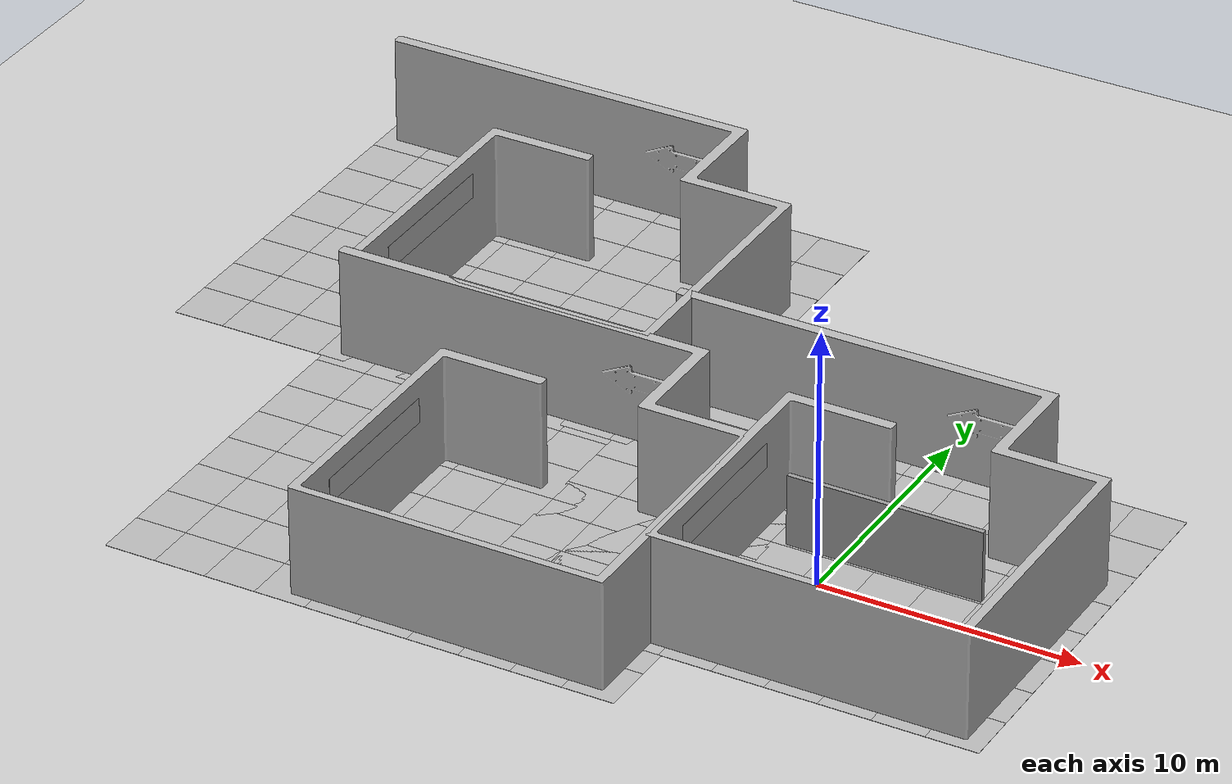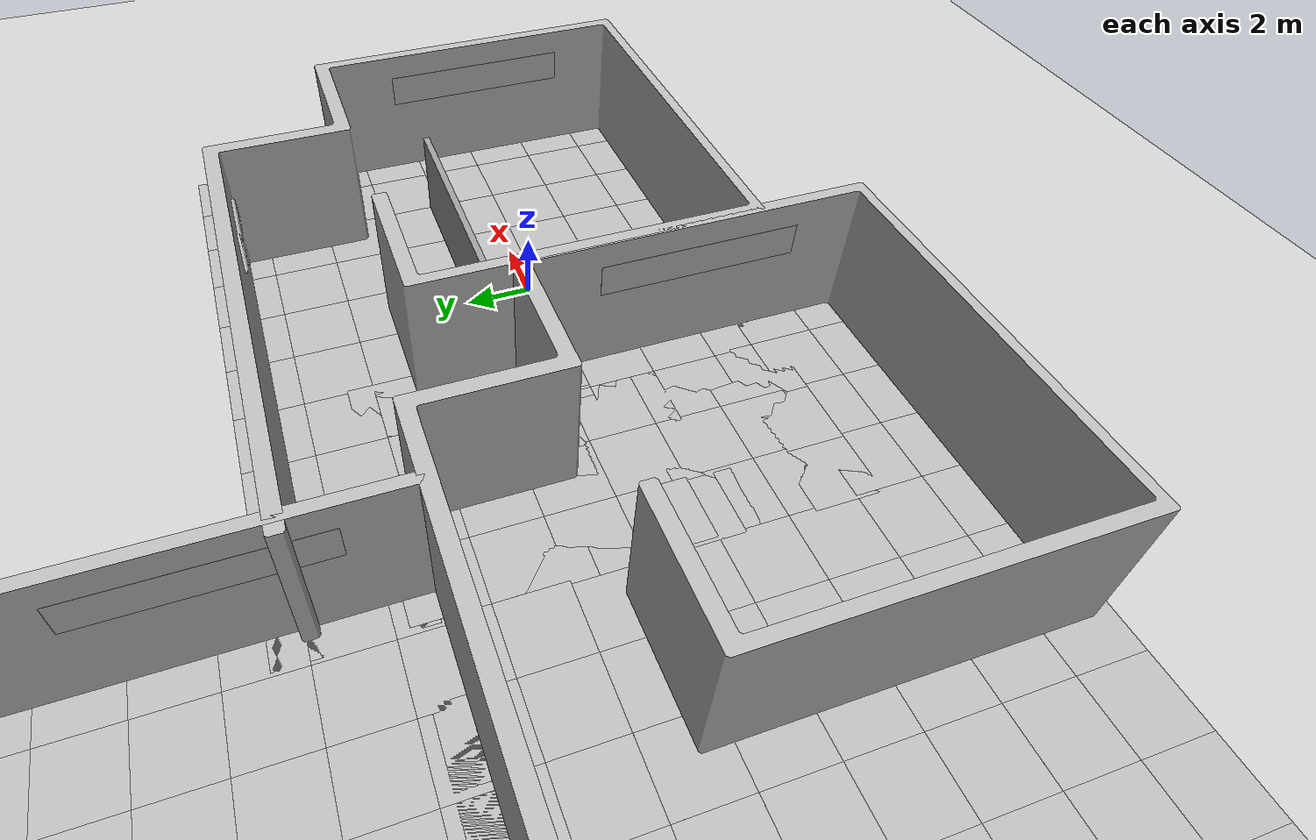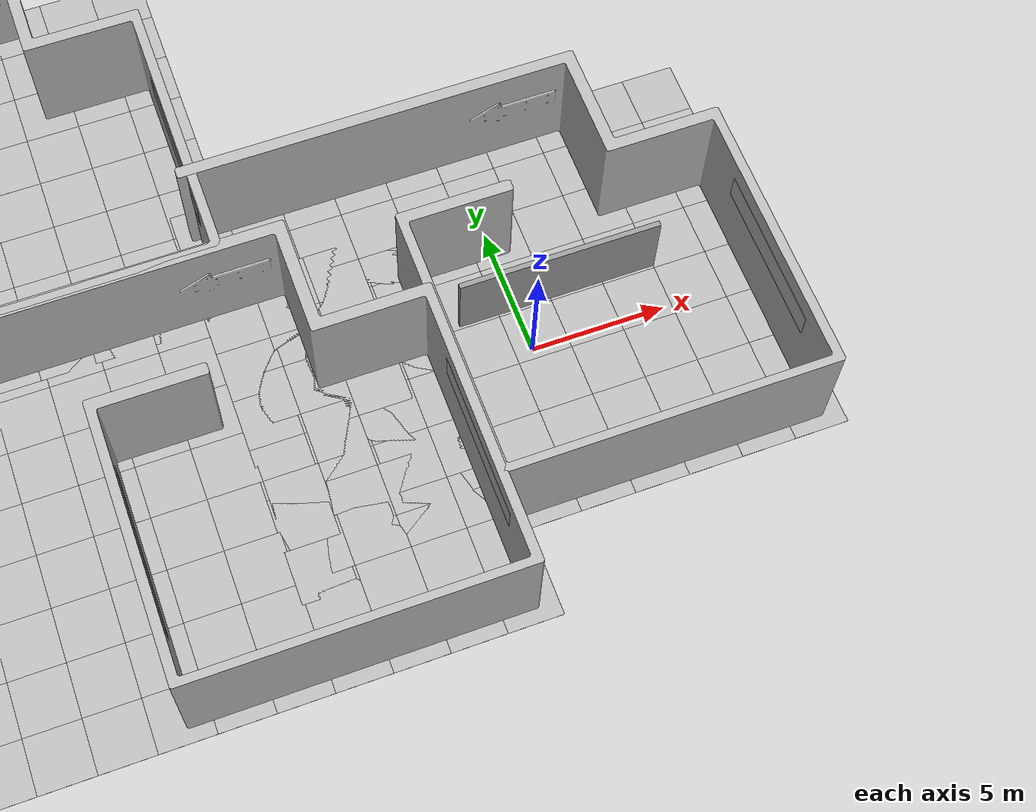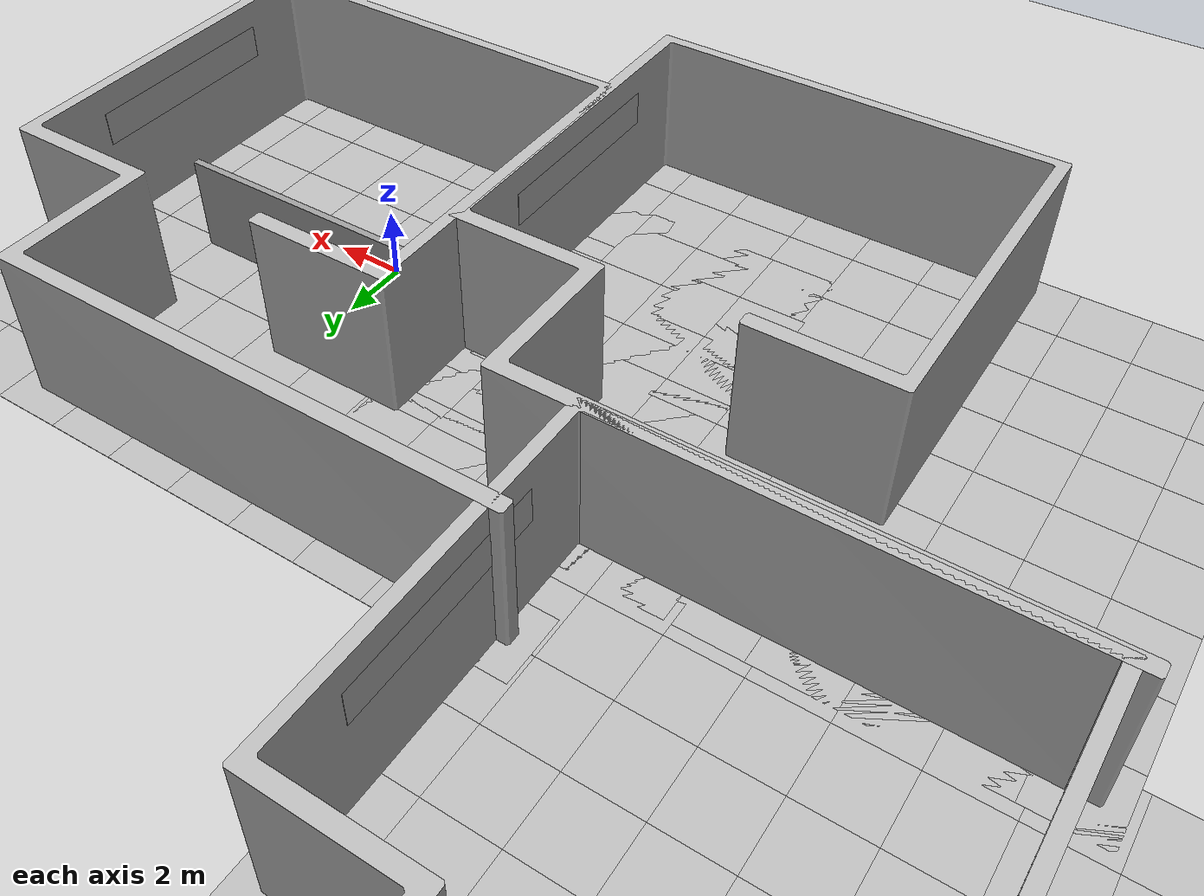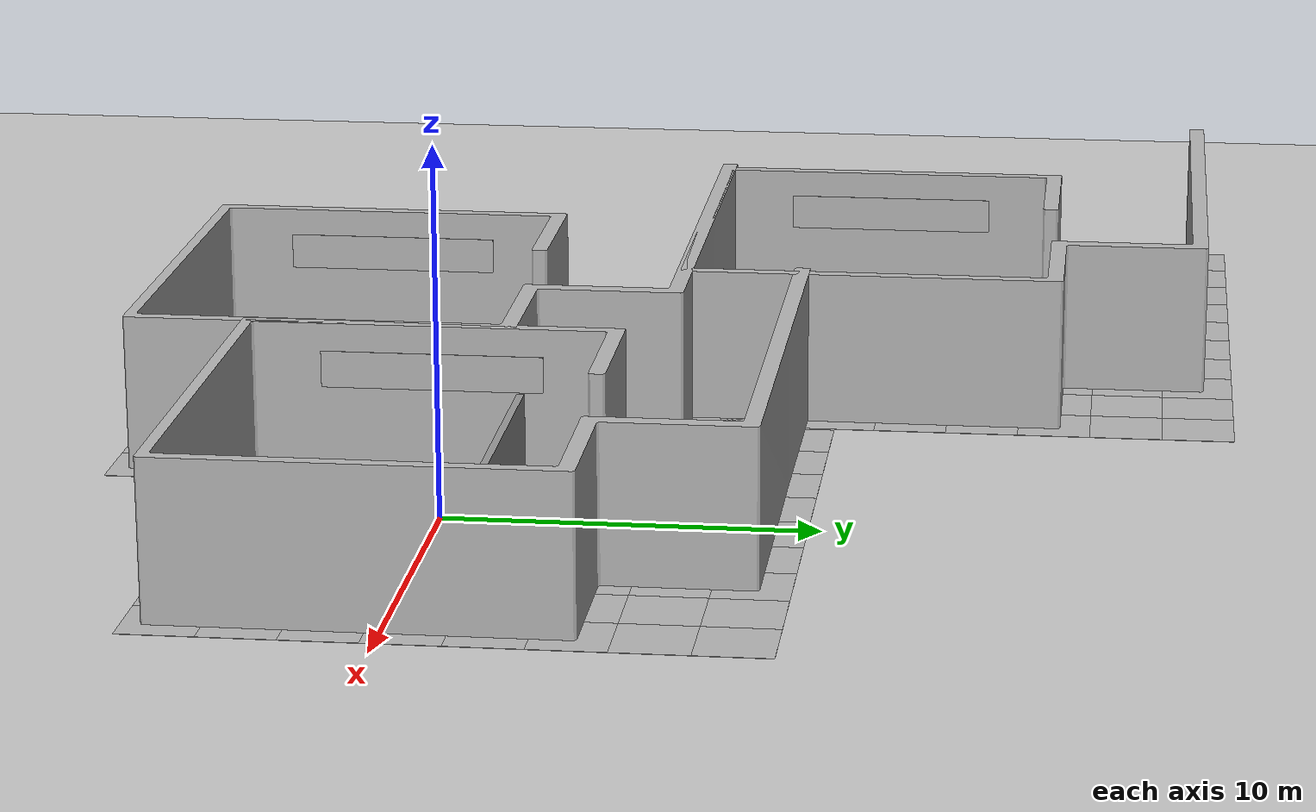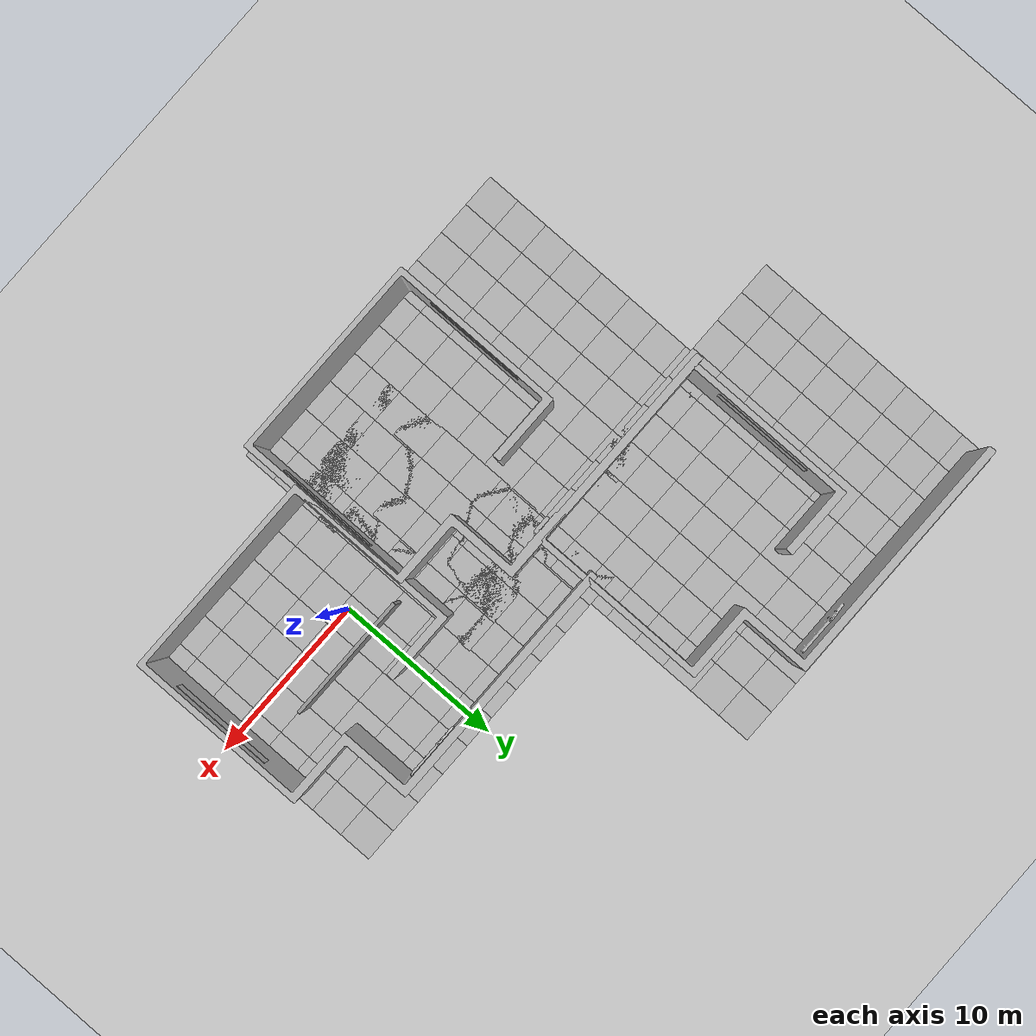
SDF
<sdf version="1.7">
 <world name="default">
  <light name="sun" type="directional">
   <pose>0 0 10 0 -0 0</pose>
   <diffuse>0.8 0.8 0.8 1</diffuse>
   <specular>0.2 0.2 0.2 1</specular>
   <attenuation>
    <range>1000</range>
    <constant>0.9</constant>
    <linear>0.01</linear>
    <quadratic>0.001</quadratic>
   </attenuation>
   <direction>-0.5 0.1 -0.9</direction>
   <spot><inner_angle>0</inner_angle><outer_angle>0</outer_angle><falloff>0</falloff></spot>
  </light>
  <model name="ground_plane">
   <static>1</static>
   <link name="link">
    <collision name="collision">
     <geometry><plane><normal>0 0 1</normal><size>100 100</size></plane></geometry>
     <surface>
      <contact><collide_bitmask>65535</collide_bitmask></contact>
      <friction><ode><mu>100</mu><mu2>50</mu2></ode></friction>
     </surface>
    </collision>
    <visual name="visual">
     <cast_shadows>0</cast_shadows>
     <geometry><plane><normal>0 0 1</normal><size>100 100</size></plane></geometry>
     <material>
      <script><uri>file://media/materials/scripts/gazebo.material</uri><name>Gazebo/Grey</name></script>
     </material>
    </visual>
   </link>
  </model>
  <gravity>0 0 -9.8</gravity>
  <magnetic_field>6e-06 2.3e-05 -4.2e-05</magnetic_field>
  <atmosphere type="adiabatic"/>
  <physics type="ode">
   <max_step_size>0.001</max_step_size>
   <real_time_factor>1</real_time_factor>
   <real_time_update_rate>1000</real_time_update_rate>
  </physics>
  <scene><ambient>0.4 0.4 0.4 1</ambient><background>0.7 0.7 0.7 1</background><shadows>1</shadows></scene>
  <audio><device>default</device></audio>
  <spherical_coordinates>
   <surface_model>EARTH_WGS84</surface_model>
   <latitude_deg>0</latitude_deg>
   <longitude_deg>0</longitude_deg>
   <elevation>0</elevation>
   <heading_deg>0</heading_deg>
  </spherical_coordinates>
  <model name="Starting Pen">
   <static>1</static>
   <link name="link">
    <collision name="wall_01">
     <pose>-0 0 2.14 0 -0 0</pose>
     <geometry><box><size>12.15 0.31 4.28</size></box></geometry>
    </collision>
    <collision name="wall_02">
     <pose>-5.28 14.3205 2.14 0 -0 0</pose>
     <geometry><box><size>14.8 0.46 4.28</size></box></geometry>
    </collision>
    <collision name="wall_03">
     <pose>-5.91 5 2.14 0 -0 0</pose>
     <geometry><box><size>0.385 10.3 4.28</size></box></geometry>
    </collision>
    <collision name="wall_04">
     <pose>5.91 5.161 2.14 0 -0 0</pose>
     <geometry><box><size>0.385 10.66 4.28</size></box></geometry>
    </collision>
    <collision name="wall_05">
     <pose>3.9 10.285 2.14 0 -0 0</pose>
     <geometry><box><size>4.38 0.45 4.28</size></box></geometry>
    </collision>
    <collision name="wall_06">
     <pose>-4 9.95 2.14 0 -0 0</pose>
     <geometry><box><size>4.25 0.45 4.28</size></box></geometry>
    </collision>
    <collision name="wall_07">
     <pose>1.94 12.3 2.14 0 -0 0</pose>
     <geometry><box><size>0.45 4.5 4.28</size></box></geometry>
    </collision>
    <collision name="wall_arrow">
     <pose>-0.232 14.03 2.46 0 -0 0</pose>
     <geometry><box><size>3.33 0.12 1.16</size></box></geometry>
    </collision>
    <collision name="collision_floor">
     <pose>-3.21 7.355 0 0 -0 0</pose>
     <geometry><box><size>20 16 0.01</size></box></geometry>
     <surface><friction><ode><mu>100</mu><mu2>50</mu2></ode></friction></surface>
    </collision>
    <visual name="visual_osrf">
     <pose>-5.74 4.99 3 0 -0 0</pose>
     <geometry><box><size>0.01 6 1</size></box></geometry>
     <material>
      <script>
       <uri>model://starting_pen/materials/scripts</uri>
       <uri>model://starting_pen/materials/textures</uri>
       <name>StartingPen/OSRF</name>
      </script>
     </material>
    </visual>
    <visual name="visual_osrf_2">
     <pose>5.74 4.99 3 0 -0 0</pose>
     <geometry><box><size>0.01 6 1</size></box></geometry>
     <material>
      <script>
       <uri>model://starting_pen/materials/scripts</uri>
       <uri>model://starting_pen/materials/textures</uri>
       <name>StartingPen/OSRF</name>
      </script>
     </material>
    </visual>
    <visual name="visual">
     <geometry><mesh><uri>model://starting_pen/meshes/starting_pen.dae</uri></mesh></geometry>
    </visual>
    <visual name="visual_floor_0">
     <pose>-12.21 0.35 0 0 -0 0</pose>
     <geometry><box><size>2 2 0.01</size></box></geometry>
     <material>
      <script>
       <uri>model://starting_pen/materials/scripts</uri>
       <uri>model://starting_pen/materials/textures</uri>
       <name>StartingPen/Floor</name>
      </script>
     </material>
    </visual>
    <visual name="visual_floor_1">
     <pose>-10.21 0.35 0 0 -0 0</pose>
     <geometry><box><size>2 2 0.01</size></box></geometry>
     <material>
      <script>
       <uri>model://starting_pen/materials/scripts</uri>
       <uri>model://starting_pen/materials/textures</uri>
       <name>StartingPen/Floor</name>
      </script>
     </material>
    </visual>
    <visual name="visual_floor_2">
     <pose>-8.21 0.35 0 0 -0 0</pose>
     <geometry><box><size>2 2 0.01</size></box></geometry>
     <material>
      <script>
       <uri>model://starting_pen/materials/scripts</uri>
       <uri>model://starting_pen/materials/textures</uri>
       <name>StartingPen/Floor</name>
      </script>
     </material>
    </visual>
    <visual name="visual_floor_3">
     <pose>-6.21 0.35 0 0 -0 0</pose>
     <geometry><box><size>2 2 0.01</size></box></geometry>
     <material>
      <script>
       <uri>model://starting_pen/materials/scripts</uri>
       <uri>model://starting_pen/materials/textures</uri>
       <name>StartingPen/Floor</name>
      </script>
     </material>
    </visual>
    <visual name="visual_floor_4">
     <pose>-4.21 0.35 0 0 -0 0</pose>
     <geometry><box><size>2 2 0.01</size></box></geometry>
     <material>
      <script>
       <uri>model://starting_pen/materials/scripts</uri>
       <uri>model://starting_pen/materials/textures</uri>
       <name>StartingPen/Floor</name>
      </script>
     </material>
    </visual>
    <visual name="visual_floor_5">
     <pose>-2.21 0.35 0 0 -0 0</pose>
     <geometry><box><size>2 2 0.01</size></box></geometry>
     <material>
      <script>
       <uri>model://starting_pen/materials/scripts</uri>
       <uri>model://starting_pen/materials/textures</uri>
       <name>StartingPen/Floor</name>
      </script>
     </material>
    </visual>
    <visual name="visual_floor_6">
     <pose>-0.21 0.35 0 0 -0 0</pose>
     <geometry><box><size>2 2 0.01</size></box></geometry>
     <material>
      <script>
       <uri>model://starting_pen/materials/scripts</uri>
       <uri>model://starting_pen/materials/textures</uri>
       <name>StartingPen/Floor</name>
      </script>
     </material>
    </visual>
    <visual name="visual_floor_7">
     <pose>1.79 0.35 0 0 -0 1.5707</pose>
     <geometry><box><size>2 2 0.01</size></box></geometry>
     <material>
      <script>
       <uri>model://starting_pen/materials/scripts</uri>
       <uri>model://starting_pen/materials/textures</uri>
       <name>StartingPen/FloorStripped</name>
      </script>
     </material>
    </visual>
    <visual name="visual_floor_8">
     <pose>3.79 0.35 0 0 -0 0</pose>
     <geometry><box><size>2 2 0.01</size></box></geometry>
     <material>
      <script>
       <uri>model://starting_pen/materials/scripts</uri>
       <uri>model://starting_pen/materials/textures</uri>
       <name>StartingPen/Floor</name>
      </script>
     </material>
    </visual>
    <visual name="visual_floor_9">
     <pose>5.79 0.35 0 0 -0 0</pose>
     <geometry><box><size>2 2 0.01</size></box></geometry>
     <material>
      <script>
       <uri>model://starting_pen/materials/scripts</uri>
       <uri>model://starting_pen/materials/textures</uri>
       <name>StartingPen/Floor</name>
      </script>
     </material>
    </visual>
    <visual name="visual_floor_10">
     <pose>-12.21 2.35 0 0 -0 1.5707</pose>
     <geometry><box><size>2 2 0.01</size></box></geometry>
     <material>
      <script>
       <uri>model://starting_pen/materials/scripts</uri>
       <uri>model://starting_pen/materials/textures</uri>
       <name>StartingPen/FloorStripped</name>
      </script>
     </material>
    </visual>
    <visual name="visual_floor_11">
     <pose>-10.21 2.35 0 0 -0 0</pose>
     <geometry><box><size>2 2 0.01</size></box></geometry>
     <material>
      <script>
       <uri>model://starting_pen/materials/scripts</uri>
       <uri>model://starting_pen/materials/textures</uri>
       <name>StartingPen/Floor</name>
      </script>
     </material>
    </visual>
    <visual name="visual_floor_12">
     <pose>-8.21 2.35 0 0 -0 0</pose>
     <geometry><box><size>2 2 0.01</size></box></geometry>
     <material>
      <script>
       <uri>model://starting_pen/materials/scripts</uri>
       <uri>model://starting_pen/materials/textures</uri>
       <name>StartingPen/Floor</name>
      </script>
     </material>
    </visual>
    <visual name="visual_floor_13">
     <pose>-6.21 2.35 0 0 -0 0</pose>
     <geometry><box><size>2 2 0.01</size></box></geometry>
     <material>
      <script>
       <uri>model://starting_pen/materials/scripts</uri>
       <uri>model://starting_pen/materials/textures</uri>
       <name>StartingPen/Floor</name>
      </script>
     </material>
    </visual>
    <visual name="visual_floor_14">
     <pose>-4.21 2.35 0 0 -0 0</pose>
     <geometry><box><size>2 2 0.01</size></box></geometry>
     <material>
      <script>
       <uri>model://starting_pen/materials/scripts</uri>
       <uri>model://starting_pen/materials/textures</uri>
       <name>StartingPen/Floor</name>
      </script>
     </material>
    </visual>
    <visual name="visual_floor_15">
     <pose>-2.21 2.35 0 0 -0 0</pose>
     <geometry><box><size>2 2 0.01</size></box></geometry>
     <material>
      <script>
       <uri>model://starting_pen/materials/scripts</uri>
       <uri>model://starting_pen/materials/textures</uri>
       <name>StartingPen/Floor</name>
      </script>
     </material>
    </visual>
    <visual name="visual_floor_16">
     <pose>-0.21 2.35 0 0 -0 1.5707</pose>
     <geometry><box><size>2 2 0.01</size></box></geometry>
     <material>
      <script>
       <uri>model://starting_pen/materials/scripts</uri>
       <uri>model://starting_pen/materials/textures</uri>
       <name>StartingPen/FloorStripped</name>
      </script>
     </material>
    </visual>
    <visual name="visual_floor_17">
     <pose>1.79 2.35 0 0 -0 1.5707</pose>
     <geometry><box><size>2 2 0.01</size></box></geometry>
     <material>
      <script>
       <uri>model://starting_pen/materials/scripts</uri>
       <uri>model://starting_pen/materials/textures</uri>
       <name>StartingPen/Floor</name>
      </script>
     </material>
    </visual>
    <visual name="visual_floor_18">
     <pose>3.79 2.35 0 0 -0 0</pose>
     <geometry><box><size>2 2 0.01</size></box></geometry>
     <material>
      <script>
       <uri>model://starting_pen/materials/scripts</uri>
       <uri>model://starting_pen/materials/textures</uri>
       <name>StartingPen/Floor</name>
      </script>
     </material>
    </visual>
    <visual name="visual_floor_19">
     <pose>5.79 2.35 0 0 -0 0</pose>
     <geometry><box><size>2 2 0.01</size></box></geometry>
     <material>
      <script>
       <uri>model://starting_pen/materials/scripts</uri>
       <uri>model://starting_pen/materials/textures</uri>
       <name>StartingPen/Floor</name>
      </script>
     </material>
    </visual>
    <visual name="visual_floor_20">
     <pose>-12.21 4.35 0 0 -0 0</pose>
     <geometry><box><size>2 2 0.01</size></box></geometry>
     <material>
      <script>
       <uri>model://starting_pen/materials/scripts</uri>
       <uri>model://starting_pen/materials/textures</uri>
       <name>StartingPen/Floor</name>
      </script>
     </material>
    </visual>
    <visual name="visual_floor_21">
     <pose>-10.21 4.35 0 0 -0 0</pose>
     <geometry><box><size>2 2 0.01</size></box></geometry>
     <material>
      <script>
       <uri>model://starting_pen/materials/scripts</uri>
       <uri>model://starting_pen/materials/textures</uri>
       <name>StartingPen/Floor</name>
      </script>
     </material>
    </visual>
    <visual name="visual_floor_22">
     <pose>-8.21 4.35 0 0 -0 1.5707</pose>
     <geometry><box><size>2 2 0.01</size></box></geometry>
     <material>
      <script>
       <uri>model://starting_pen/materials/scripts</uri>
       <uri>model://starting_pen/materials/textures</uri>
       <name>StartingPen/FloorStripped</name>
      </script>
     </material>
    </visual>
    <visual name="visual_floor_23">
     <pose>-6.21 4.35 0 0 -0 0</pose>
     <geometry><box><size>2 2 0.01</size></box></geometry>
     <material>
      <script>
       <uri>model://starting_pen/materials/scripts</uri>
       <uri>model://starting_pen/materials/textures</uri>
       <name>StartingPen/Floor</name>
      </script>
     </material>
    </visual>
    <visual name="visual_floor_24">
     <pose>-4.21 4.35 0 0 -0 0</pose>
     <geometry><box><size>2 2 0.01</size></box></geometry>
     <material>
      <script>
       <uri>model://starting_pen/materials/scripts</uri>
       <uri>model://starting_pen/materials/textures</uri>
       <name>StartingPen/Floor</name>
      </script>
     </material>
    </visual>
    <visual name="visual_floor_25">
     <pose>-2.21 4.35 0 0 -0 0</pose>
     <geometry><box><size>2 2 0.01</size></box></geometry>
     <material>
      <script>
       <uri>model://starting_pen/materials/scripts</uri>
       <uri>model://starting_pen/materials/textures</uri>
       <name>StartingPen/Floor</name>
      </script>
     </material>
    </visual>
    <visual name="visual_floor_26">
     <pose>-0.21 4.35 0 0 -0 0</pose>
     <geometry><box><size>2 2 0.01</size></box></geometry>
     <material>
      <script>
       <uri>model://starting_pen/materials/scripts</uri>
       <uri>model://starting_pen/materials/textures</uri>
       <name>StartingPen/Floor</name>
      </script>
     </material>
    </visual>
    <visual name="visual_floor_27">
     <pose>1.79 4.35 0 0 -0 0</pose>
     <geometry><box><size>2 2 0.01</size></box></geometry>
     <material>
      <script>
       <uri>model://starting_pen/materials/scripts</uri>
       <uri>model://starting_pen/materials/textures</uri>
       <name>StartingPen/Floor</name>
      </script>
     </material>
    </visual>
    <visual name="visual_floor_28">
     <pose>3.79 4.35 0 0 -0 0</pose>
     <geometry><box><size>2 2 0.01</size></box></geometry>
     <material>
      <script>
       <uri>model://starting_pen/materials/scripts</uri>
       <uri>model://starting_pen/materials/textures</uri>
       <name>StartingPen/Floor</name>
      </script>
     </material>
    </visual>
    <visual name="visual_floor_29">
     <pose>5.79 4.35 0 0 -0 1.5707</pose>
     <geometry><box><size>2 2 0.01</size></box></geometry>
     <material>
      <script>
       <uri>model://starting_pen/materials/scripts</uri>
       <uri>model://starting_pen/materials/textures</uri>
       <name>StartingPen/FloorStripped</name>
      </script>
     </material>
    </visual>
    <visual name="visual_floor_30">
     <pose>-12.21 6.35 0 0 -0 0</pose>
     <geometry><box><size>2 2 0.01</size></box></geometry>
     <material>
      <script>
       <uri>model://starting_pen/materials/scripts</uri>
       <uri>model://starting_pen/materials/textures</uri>
       <name>StartingPen/Floor</name>
      </script>
     </material>
    </visual>
    <visual name="visual_floor_31">
     <pose>-10.21 6.35 0 0 -0 0</pose>
     <geometry><box><size>2 2 0.01</size></box></geometry>
     <material>
      <script>
       <uri>model://starting_pen/materials/scripts</uri>
       <uri>model://starting_pen/materials/textures</uri>
       <name>StartingPen/Floor</name>
      </script>
     </material>
    </visual>
    <visual name="visual_floor_32">
     <pose>-8.21 6.35 0 0 -0 0</pose>
     <geometry><box><size>2 2 0.01</size></box></geometry>
     <material>
      <script>
       <uri>model://starting_pen/materials/scripts</uri>
       <uri>model://starting_pen/materials/textures</uri>
       <name>StartingPen/Floor</name>
      </script>
     </material>
    </visual>
    <visual name="visual_floor_33">
     <pose>-6.21 6.35 0 0 -0 1.5707</pose>
     <geometry><box><size>2 2 0.01</size></box></geometry>
     <material>
      <script>
       <uri>model://starting_pen/materials/scripts</uri>
       <uri>model://starting_pen/materials/textures</uri>
       <name>StartingPen/FloorStripped</name>
      </script>
     </material>
    </visual>
    <visual name="visual_floor_34">
     <pose>-4.21 6.35 0 0 -0 0</pose>
     <geometry><box><size>2 2 0.01</size></box></geometry>
     <material>
      <script>
       <uri>model://starting_pen/materials/scripts</uri>
       <uri>model://starting_pen/materials/textures</uri>
       <name>StartingPen/Floor</name>
      </script>
     </material>
    </visual>
    <visual name="visual_floor_35">
     <pose>-2.21 6.35 0 0 -0 1.5707</pose>
     <geometry><box><size>2 2 0.01</size></box></geometry>
     <material>
      <script>
       <uri>model://starting_pen/materials/scripts</uri>
       <uri>model://starting_pen/materials/textures</uri>
       <name>StartingPen/FloorStripped</name>
      </script>
     </material>
    </visual>
    <visual name="visual_floor_36">
     <pose>-0.21 6.35 0 0 -0 0</pose>
     <geometry><box><size>2 2 0.01</size></box></geometry>
     <material>
      <script>
       <uri>model://starting_pen/materials/scripts</uri>
       <uri>model://starting_pen/materials/textures</uri>
       <name>StartingPen/Floor</name>
      </script>
     </material>
    </visual>
    <visual name="visual_floor_37">
     <pose>1.79 6.35 0 0 -0 0</pose>
     <geometry><box><size>2 2 0.01</size></box></geometry>
     <material>
      <script>
       <uri>model://starting_pen/materials/scripts</uri>
       <uri>model://starting_pen/materials/textures</uri>
       <name>StartingPen/Floor</name>
      </script>
     </material>
    </visual>
    <visual name="visual_floor_38">
     <pose>3.79 6.35 0 0 -0 0</pose>
     <geometry><box><size>2 2 0.01</size></box></geometry>
     <material>
      <script>
       <uri>model://starting_pen/materials/scripts</uri>
       <uri>model://starting_pen/materials/textures</uri>
       <name>StartingPen/Floor</name>
      </script>
     </material>
    </visual>
    <visual name="visual_floor_39">
     <pose>5.79 6.35 0 0 -0 0</pose>
     <geometry><box><size>2 2 0.01</size></box></geometry>
     <material>
      <script>
       <uri>model://starting_pen/materials/scripts</uri>
       <uri>model://starting_pen/materials/textures</uri>
       <name>StartingPen/Floor</name>
      </script>
     </material>
    </visual>
    <visual name="visual_floor_40">
     <pose>-12.21 8.35 0 0 -0 0</pose>
     <geometry><box><size>2 2 0.01</size></box></geometry>
     <material>
      <script>
       <uri>model://starting_pen/materials/scripts</uri>
       <uri>model://starting_pen/materials/textures</uri>
       <name>StartingPen/Floor</name>
      </script>
     </material>
    </visual>
    <visual name="visual_floor_41">
     <pose>-10.21 8.35 0 0 -0 0</pose>
     <geometry><box><size>2 2 0.01</size></box></geometry>
     <material>
      <script>
       <uri>model://starting_pen/materials/scripts</uri>
       <uri>model://starting_pen/materials/textures</uri>
       <name>StartingPen/Floor</name>
      </script>
     </material>
    </visual>
    <visual name="visual_floor_42">
     <pose>-8.21 8.35 0 0 -0 1.5707</pose>
     <geometry><box><size>2 2 0.01</size></box></geometry>
     <material>
      <script>
       <uri>model://starting_pen/materials/scripts</uri>
       <uri>model://starting_pen/materials/textures</uri>
       <name>StartingPen/FloorStripped</name>
      </script>
     </material>
    </visual>
    <visual name="visual_floor_43">
     <pose>-6.21 8.35 0 0 -0 0</pose>
     <geometry><box><size>2 2 0.01</size></box></geometry>
     <material>
      <script>
       <uri>model://starting_pen/materials/scripts</uri>
       <uri>model://starting_pen/materials/textures</uri>
       <name>StartingPen/Floor</name>
      </script>
     </material>
    </visual>
    <visual name="visual_floor_44">
     <pose>-4.21 8.35 0 0 -0 0</pose>
     <geometry><box><size>2 2 0.01</size></box></geometry>
     <material>
      <script>
       <uri>model://starting_pen/materials/scripts</uri>
       <uri>model://starting_pen/materials/textures</uri>
       <name>StartingPen/Floor</name>
      </script>
     </material>
    </visual>
    <visual name="visual_floor_45">
     <pose>-2.21 8.35 0 0 -0 0</pose>
     <geometry><box><size>2 2 0.01</size></box></geometry>
     <material>
      <script>
       <uri>model://starting_pen/materials/scripts</uri>
       <uri>model://starting_pen/materials/textures</uri>
       <name>StartingPen/Floor</name>
      </script>
     </material>
    </visual>
    <visual name="visual_floor_46">
     <pose>-0.21 8.35 0 0 -0 1.5707</pose>
     <geometry><box><size>2 2 0.01</size></box></geometry>
     <material>
      <script>
       <uri>model://starting_pen/materials/scripts</uri>
       <uri>model://starting_pen/materials/textures</uri>
       <name>StartingPen/FloorStripped</name>
      </script>
     </material>
    </visual>
    <visual name="visual_floor_47">
     <pose>1.79 8.35 0 0 -0 0</pose>
     <geometry><box><size>2 2 0.01</size></box></geometry>
     <material>
      <script>
       <uri>model://starting_pen/materials/scripts</uri>
       <uri>model://starting_pen/materials/textures</uri>
       <name>StartingPen/Floor</name>
      </script>
     </material>
    </visual>
    <visual name="visual_floor_48">
     <pose>3.79 8.35 0 0 -0 0</pose>
     <geometry><box><size>2 2 0.01</size></box></geometry>
     <material>
      <script>
       <uri>model://starting_pen/materials/scripts</uri>
       <uri>model://starting_pen/materials/textures</uri>
       <name>StartingPen/Floor</name>
      </script>
     </material>
    </visual>
    <visual name="visual_floor_49">
     <pose>5.79 8.35 0 0 -0 0</pose>
     <geometry><box><size>2 2 0.01</size></box></geometry>
     <material>
      <script>
       <uri>model://starting_pen/materials/scripts</uri>
       <uri>model://starting_pen/materials/textures</uri>
       <name>StartingPen/Floor</name>
      </script>
     </material>
    </visual>
    <visual name="visual_floor_50">
     <pose>-12.21 10.35 0 0 -0 0</pose>
     <geometry><box><size>2 2 0.01</size></box></geometry>
     <material>
      <script>
       <uri>model://starting_pen/materials/scripts</uri>
       <uri>model://starting_pen/materials/textures</uri>
       <name>StartingPen/Floor</name>
      </script>
     </material>
    </visual>
    <visual name="visual_floor_51">
     <pose>-10.21 10.35 0 0 -0 0</pose>
     <geometry><box><size>2 2 0.01</size></box></geometry>
     <material>
      <script>
       <uri>model://starting_pen/materials/scripts</uri>
       <uri>model://starting_pen/materials/textures</uri>
       <name>StartingPen/Floor</name>
      </script>
     </material>
    </visual>
    <visual name="visual_floor_52">
     <pose>-8.21 10.35 0 0 -0 0</pose>
     <geometry><box><size>2 2 0.01</size></box></geometry>
     <material>
      <script>
       <uri>model://starting_pen/materials/scripts</uri>
       <uri>model://starting_pen/materials/textures</uri>
       <name>StartingPen/Floor</name>
      </script>
     </material>
    </visual>
    <visual name="visual_floor_53">
     <pose>-6.21 10.35 0 0 -0 1.5707</pose>
     <geometry><box><size>2 2 0.01</size></box></geometry>
     <material>
      <script>
       <uri>model://starting_pen/materials/scripts</uri>
       <uri>model://starting_pen/materials/textures</uri>
       <name>StartingPen/FloorStripped</name>
      </script>
     </material>
    </visual>
    <visual name="visual_floor_54">
     <pose>-4.21 10.35 0 0 -0 0</pose>
     <geometry><box><size>2 2 0.01</size></box></geometry>
     <material>
      <script>
       <uri>model://starting_pen/materials/scripts</uri>
       <uri>model://starting_pen/materials/textures</uri>
       <name>StartingPen/Floor</name>
      </script>
     </material>
    </visual>
    <visual name="visual_floor_55">
     <pose>-2.21 10.35 0 0 -0 0</pose>
     <geometry><box><size>2 2 0.01</size></box></geometry>
     <material>
      <script>
       <uri>model://starting_pen/materials/scripts</uri>
       <uri>model://starting_pen/materials/textures</uri>
       <name>StartingPen/Floor</name>
      </script>
     </material>
    </visual>
    <visual name="visual_floor_56">
     <pose>-0.21 10.35 0 0 -0 0</pose>
     <geometry><box><size>2 2 0.01</size></box></geometry>
     <material>
      <script>
       <uri>model://starting_pen/materials/scripts</uri>
       <uri>model://starting_pen/materials/textures</uri>
       <name>StartingPen/Floor</name>
      </script>
     </material>
    </visual>
    <visual name="visual_floor_57">
     <pose>1.79 10.35 0 0 -0 0</pose>
     <geometry><box><size>2 2 0.01</size></box></geometry>
     <material>
      <script>
       <uri>model://starting_pen/materials/scripts</uri>
       <uri>model://starting_pen/materials/textures</uri>
       <name>StartingPen/Floor</name>
      </script>
     </material>
    </visual>
    <visual name="visual_floor_58">
     <pose>3.79 10.35 0 0 -0 0</pose>
     <geometry><box><size>2 2 0.01</size></box></geometry>
     <material>
      <script>
       <uri>model://starting_pen/materials/scripts</uri>
       <uri>model://starting_pen/materials/textures</uri>
       <name>StartingPen/Floor</name>
      </script>
     </material>
    </visual>
    <visual name="visual_floor_59">
     <pose>5.79 10.35 0 0 -0 0</pose>
     <geometry><box><size>2 2 0.01</size></box></geometry>
     <material>
      <script>
       <uri>model://starting_pen/materials/scripts</uri>
       <uri>model://starting_pen/materials/textures</uri>
       <name>StartingPen/Floor</name>
      </script>
     </material>
    </visual>
    <visual name="visual_floor_60">
     <pose>-12.21 12.35 0 0 -0 1.5707</pose>
     <geometry><box><size>2 2 0.01</size></box></geometry>
     <material>
      <script>
       <uri>model://starting_pen/materials/scripts</uri>
       <uri>model://starting_pen/materials/textures</uri>
       <name>StartingPen/FloorStripped</name>
      </script>
     </material>
    </visual>
    <visual name="visual_floor_61">
     <pose>-10.21 12.35 0 0 -0 0</pose>
     <geometry><box><size>2 2 0.01</size></box></geometry>
     <material>
      <script>
       <uri>model://starting_pen/materials/scripts</uri>
       <uri>model://starting_pen/materials/textures</uri>
       <name>StartingPen/Floor</name>
      </script>
     </material>
    </visual>
    <visual name="visual_floor_62">
     <pose>-8.21 12.35 0 0 -0 0</pose>
     <geometry><box><size>2 2 0.01</size></box></geometry>
     <material>
      <script>
       <uri>model://starting_pen/materials/scripts</uri>
       <uri>model://starting_pen/materials/textures</uri>
       <name>StartingPen/Floor</name>
      </script>
     </material>
    </visual>
    <visual name="visual_floor_63">
     <pose>-6.21 12.35 0 0 -0 0</pose>
     <geometry><box><size>2 2 0.01</size></box></geometry>
     <material>
      <script>
       <uri>model://starting_pen/materials/scripts</uri>
       <uri>model://starting_pen/materials/textures</uri>
       <name>StartingPen/Floor</name>
      </script>
     </material>
    </visual>
    <visual name="visual_floor_64">
     <pose>-4.21 12.35 0 0 -0 0</pose>
     <geometry><box><size>2 2 0.01</size></box></geometry>
     <material>
      <script>
       <uri>model://starting_pen/materials/scripts</uri>
       <uri>model://starting_pen/materials/textures</uri>
       <name>StartingPen/Floor</name>
      </script>
     </material>
    </visual>
    <visual name="visual_floor_65">
     <pose>-2.21 12.35 0 0 -0 1.5707</pose>
     <geometry><box><size>2 2 0.01</size></box></geometry>
     <material>
      <script>
       <uri>model://starting_pen/materials/scripts</uri>
       <uri>model://starting_pen/materials/textures</uri>
       <name>StartingPen/FloorStripped</name>
      </script>
     </material>
    </visual>
    <visual name="visual_floor_66">
     <pose>-0.21 12.35 0 0 -0 0</pose>
     <geometry><box><size>2 2 0.01</size></box></geometry>
     <material>
      <script>
       <uri>model://starting_pen/materials/scripts</uri>
       <uri>model://starting_pen/materials/textures</uri>
       <name>StartingPen/Floor</name>
      </script>
     </material>
    </visual>
    <visual name="visual_floor_67">
     <pose>1.79 12.35 0 0 -0 0</pose>
     <geometry><box><size>2 2 0.01</size></box></geometry>
     <material>
      <script>
       <uri>model://starting_pen/materials/scripts</uri>
       <uri>model://starting_pen/materials/textures</uri>
       <name>StartingPen/Floor</name>
      </script>
     </material>
    </visual>
    <visual name="visual_floor_68">
     <pose>3.79 12.35 0 0 -0 0</pose>
     <geometry><box><size>2 2 0.01</size></box></geometry>
     <material>
      <script>
       <uri>model://starting_pen/materials/scripts</uri>
       <uri>model://starting_pen/materials/textures</uri>
       <name>StartingPen/Floor</name>
      </script>
     </material>
    </visual>
    <visual name="visual_floor_69">
     <pose>5.79 12.35 0 0 -0 0</pose>
     <geometry><box><size>2 2 0.01</size></box></geometry>
     <material>
      <script>
       <uri>model://starting_pen/materials/scripts</uri>
       <uri>model://starting_pen/materials/textures</uri>
       <name>StartingPen/Floor</name>
      </script>
     </material>
    </visual>
    <visual name="visual_floor_70">
     <pose>-12.21 14.35 0 0 -0 0</pose>
     <geometry><box><size>2 2 0.01</size></box></geometry>
     <material>
      <script>
       <uri>model://starting_pen/materials/scripts</uri>
       <uri>model://starting_pen/materials/textures</uri>
       <name>StartingPen/Floor</name>
      </script>
     </material>
    </visual>
    <visual name="visual_floor_71">
     <pose>-10.21 14.35 0 0 -0 0</pose>
     <geometry><box><size>2 2 0.01</size></box></geometry>
     <material>
      <script>
       <uri>model://starting_pen/materials/scripts</uri>
       <uri>model://starting_pen/materials/textures</uri>
       <name>StartingPen/Floor</name>
      </script>
     </material>
    </visual>
    <visual name="visual_floor_72">
     <pose>-8.21 14.35 0 0 -0 0</pose>
     <geometry><box><size>2 2 0.01</size></box></geometry>
     <material>
      <script>
       <uri>model://starting_pen/materials/scripts</uri>
       <uri>model://starting_pen/materials/textures</uri>
       <name>StartingPen/Floor</name>
      </script>
     </material>
    </visual>
    <visual name="visual_floor_73">
     <pose>-6.21 14.35 0 0 -0 0</pose>
     <geometry><box><size>2 2 0.01</size></box></geometry>
     <material>
      <script>
       <uri>model://starting_pen/materials/scripts</uri>
       <uri>model://starting_pen/materials/textures</uri>
       <name>StartingPen/Floor</name>
      </script>
     </material>
    </visual>
    <visual name="visual_floor_74">
     <pose>-4.21 14.35 0 0 -0 1.5707</pose>
     <geometry><box><size>2 2 0.01</size></box></geometry>
     <material>
      <script>
       <uri>model://starting_pen/materials/scripts</uri>
       <uri>model://starting_pen/materials/textures</uri>
       <name>StartingPen/FloorStripped</name>
      </script>
     </material>
    </visual>
    <visual name="visual_floor_75">
     <pose>-2.21 14.35 0 0 -0 1.5707</pose>
     <geometry><box><size>2 2 0.01</size></box></geometry>
     <material>
      <script>
       <uri>model://starting_pen/materials/scripts</uri>
       <uri>model://starting_pen/materials/textures</uri>
       <name>StartingPen/Floor</name>
      </script>
     </material>
    </visual>
    <visual name="visual_floor_76">
     <pose>-0.21 14.35 0 0 -0 0</pose>
     <geometry><box><size>2 2 0.01</size></box></geometry>
     <material>
      <script>
       <uri>model://starting_pen/materials/scripts</uri>
       <uri>model://starting_pen/materials/textures</uri>
       <name>StartingPen/Floor</name>
      </script>
     </material>
    </visual>
    <visual name="visual_floor_77">
     <pose>1.79 14.35 0 0 -0 0</pose>
     <geometry><box><size>2 2 0.01</size></box></geometry>
     <material>
      <script>
       <uri>model://starting_pen/materials/scripts</uri>
       <uri>model://starting_pen/materials/textures</uri>
       <name>StartingPen/Floor</name>
      </script>
     </material>
    </visual>
    <visual name="visual_floor_78">
     <pose>3.79 14.35 0 0 -0 0</pose>
     <geometry><box><size>2 2 0.01</size></box></geometry>
     <material>
      <script>
       <uri>model://starting_pen/materials/scripts</uri>
       <uri>model://starting_pen/materials/textures</uri>
       <name>StartingPen/FloorStripped</name>
      </script>
     </material>
    </visual>
    <visual name="visual_floor_79">
     <pose>5.79 14.35 0 0 -0 0</pose>
     <geometry><box><size>2 2 0.01</size></box></geometry>
     <material>
      <script>
       <uri>model://starting_pen/materials/scripts</uri>
       <uri>model://starting_pen/materials/textures</uri>
       <name>StartingPen/Floor</name>
      </script>
     </material>
    </visual>
   </link>
   <pose>2.54673 -5.71206 0 0 -0 0</pose>
  </model>
  <model name="Starting Pen_0">
   <static>1</static>
   <link name="link">
    <collision name="wall_01">
     <pose>-0 0 2.14 0 -0 0</pose>
     <geometry><box><size>12.15 0.31 4.28</size></box></geometry>
    </collision>
    <collision name="wall_02">
     <pose>-5.28 14.3205 2.14 0 -0 0</pose>
     <geometry><box><size>14.8 0.46 4.28</size></box></geometry>
    </collision>
    <collision name="wall_03">
     <pose>-5.91 5 2.14 0 -0 0</pose>
     <geometry><box><size>0.385 10.3 4.28</size></box></geometry>
    </collision>
    <collision name="wall_04">
     <pose>5.91 5.161 2.14 0 -0 0</pose>
     <geometry><box><size>0.385 10.66 4.28</size></box></geometry>
    </collision>
    <collision name="wall_05">
     <pose>3.9 10.285 2.14 0 -0 0</pose>
     <geometry><box><size>4.38 0.45 4.28</size></box></geometry>
    </collision>
    <collision name="wall_06">
     <pose>-4 9.95 2.14 0 -0 0</pose>
     <geometry><box><size>4.25 0.45 4.28</size></box></geometry>
    </collision>
    <collision name="wall_07">
     <pose>1.94 12.3 2.14 0 -0 0</pose>
     <geometry><box><size>0.45 4.5 4.28</size></box></geometry>
    </collision>
    <collision name="wall_arrow">
     <pose>-0.232 14.03 2.46 0 -0 0</pose>
     <geometry><box><size>3.33 0.12 1.16</size></box></geometry>
    </collision>
    <collision name="collision_floor">
     <pose>-3.21 7.355 0 0 -0 0</pose>
     <geometry><box><size>20 16 0.01</size></box></geometry>
     <surface><friction><ode><mu>100</mu><mu2>50</mu2></ode></friction></surface>
    </collision>
    <visual name="visual_osrf">
     <pose>-5.74 4.99 3 0 -0 0</pose>
     <geometry><box><size>0.01 6 1</size></box></geometry>
     <material>
      <script>
       <uri>model://starting_pen/materials/scripts</uri>
       <uri>model://starting_pen/materials/textures</uri>
       <name>StartingPen/OSRF</name>
      </script>
     </material>
    </visual>
    <visual name="visual_osrf_2">
     <pose>5.74 4.99 3 0 -0 0</pose>
     <geometry><box><size>0.01 6 1</size></box></geometry>
     <material>
      <script>
       <uri>model://starting_pen/materials/scripts</uri>
       <uri>model://starting_pen/materials/textures</uri>
       <name>StartingPen/OSRF</name>
      </script>
     </material>
    </visual>
    <visual name="visual">
     <geometry><mesh><uri>model://starting_pen/meshes/starting_pen.dae</uri></mesh></geometry>
    </visual>
    <visual name="visual_floor_0">
     <pose>-12.21 0.35 0 0 -0 0</pose>
     <geometry><box><size>2 2 0.01</size></box></geometry>
     <material>
      <script>
       <uri>model://starting_pen/materials/scripts</uri>
       <uri>model://starting_pen/materials/textures</uri>
       <name>StartingPen/Floor</name>
      </script>
     </material>
    </visual>
    <visual name="visual_floor_1">
     <pose>-10.21 0.35 0 0 -0 0</pose>
     <geometry><box><size>2 2 0.01</size></box></geometry>
     <material>
      <script>
       <uri>model://starting_pen/materials/scripts</uri>
       <uri>model://starting_pen/materials/textures</uri>
       <name>StartingPen/Floor</name>
      </script>
     </material>
    </visual>
    <visual name="visual_floor_2">
     <pose>-8.21 0.35 0 0 -0 0</pose>
     <geometry><box><size>2 2 0.01</size></box></geometry>
     <material>
      <script>
       <uri>model://starting_pen/materials/scripts</uri>
       <uri>model://starting_pen/materials/textures</uri>
       <name>StartingPen/Floor</name>
      </script>
     </material>
    </visual>
    <visual name="visual_floor_3">
     <pose>-6.21 0.35 0 0 -0 0</pose>
     <geometry><box><size>2 2 0.01</size></box></geometry>
     <material>
      <script>
       <uri>model://starting_pen/materials/scripts</uri>
       <uri>model://starting_pen/materials/textures</uri>
       <name>StartingPen/Floor</name>
      </script>
     </material>
    </visual>
    <visual name="visual_floor_4">
     <pose>-4.21 0.35 0 0 -0 0</pose>
     <geometry><box><size>2 2 0.01</size></box></geometry>
     <material>
      <script>
       <uri>model://starting_pen/materials/scripts</uri>
       <uri>model://starting_pen/materials/textures</uri>
       <name>StartingPen/Floor</name>
      </script>
     </material>
    </visual>
    <visual name="visual_floor_5">
     <pose>-2.21 0.35 0 0 -0 0</pose>
     <geometry><box><size>2 2 0.01</size></box></geometry>
     <material>
      <script>
       <uri>model://starting_pen/materials/scripts</uri>
       <uri>model://starting_pen/materials/textures</uri>
       <name>StartingPen/Floor</name>
      </script>
     </material>
    </visual>
    <visual name="visual_floor_6">
     <pose>-0.21 0.35 0 0 -0 0</pose>
     <geometry><box><size>2 2 0.01</size></box></geometry>
     <material>
      <script>
       <uri>model://starting_pen/materials/scripts</uri>
       <uri>model://starting_pen/materials/textures</uri>
       <name>StartingPen/Floor</name>
      </script>
     </material>
    </visual>
    <visual name="visual_floor_7">
     <pose>1.79 0.35 0 0 -0 1.5707</pose>
     <geometry><box><size>2 2 0.01</size></box></geometry>
     <material>
      <script>
       <uri>model://starting_pen/materials/scripts</uri>
       <uri>model://starting_pen/materials/textures</uri>
       <name>StartingPen/FloorStripped</name>
      </script>
     </material>
    </visual>
    <visual name="visual_floor_8">
     <pose>3.79 0.35 0 0 -0 0</pose>
     <geometry><box><size>2 2 0.01</size></box></geometry>
     <material>
      <script>
       <uri>model://starting_pen/materials/scripts</uri>
       <uri>model://starting_pen/materials/textures</uri>
       <name>StartingPen/Floor</name>
      </script>
     </material>
    </visual>
    <visual name="visual_floor_9">
     <pose>5.79 0.35 0 0 -0 0</pose>
     <geometry><box><size>2 2 0.01</size></box></geometry>
     <material>
      <script>
       <uri>model://starting_pen/materials/scripts</uri>
       <uri>model://starting_pen/materials/textures</uri>
       <name>StartingPen/Floor</name>
      </script>
     </material>
    </visual>
    <visual name="visual_floor_10">
     <pose>-12.21 2.35 0 0 -0 1.5707</pose>
     <geometry><box><size>2 2 0.01</size></box></geometry>
     <material>
      <script>
       <uri>model://starting_pen/materials/scripts</uri>
       <uri>model://starting_pen/materials/textures</uri>
       <name>StartingPen/FloorStripped</name>
      </script>
     </material>
    </visual>
    <visual name="visual_floor_11">
     <pose>-10.21 2.35 0 0 -0 0</pose>
     <geometry><box><size>2 2 0.01</size></box></geometry>
     <material>
      <script>
       <uri>model://starting_pen/materials/scripts</uri>
       <uri>model://starting_pen/materials/textures</uri>
       <name>StartingPen/Floor</name>
      </script>
     </material>
    </visual>
    <visual name="visual_floor_12">
     <pose>-8.21 2.35 0 0 -0 0</pose>
     <geometry><box><size>2 2 0.01</size></box></geometry>
     <material>
      <script>
       <uri>model://starting_pen/materials/scripts</uri>
       <uri>model://starting_pen/materials/textures</uri>
       <name>StartingPen/Floor</name>
      </script>
     </material>
    </visual>
    <visual name="visual_floor_13">
     <pose>-6.21 2.35 0 0 -0 0</pose>
     <geometry><box><size>2 2 0.01</size></box></geometry>
     <material>
      <script>
       <uri>model://starting_pen/materials/scripts</uri>
       <uri>model://starting_pen/materials/textures</uri>
       <name>StartingPen/Floor</name>
      </script>
     </material>
    </visual>
    <visual name="visual_floor_14">
     <pose>-4.21 2.35 0 0 -0 0</pose>
     <geometry><box><size>2 2 0.01</size></box></geometry>
     <material>
      <script>
       <uri>model://starting_pen/materials/scripts</uri>
       <uri>model://starting_pen/materials/textures</uri>
       <name>StartingPen/Floor</name>
      </script>
     </material>
    </visual>
    <visual name="visual_floor_15">
     <pose>-2.21 2.35 0 0 -0 0</pose>
     <geometry><box><size>2 2 0.01</size></box></geometry>
     <material>
      <script>
       <uri>model://starting_pen/materials/scripts</uri>
       <uri>model://starting_pen/materials/textures</uri>
       <name>StartingPen/Floor</name>
      </script>
     </material>
    </visual>
    <visual name="visual_floor_16">
     <pose>-0.21 2.35 0 0 -0 1.5707</pose>
     <geometry><box><size>2 2 0.01</size></box></geometry>
     <material>
      <script>
       <uri>model://starting_pen/materials/scripts</uri>
       <uri>model://starting_pen/materials/textures</uri>
       <name>StartingPen/FloorStripped</name>
      </script>
     </material>
    </visual>
    <visual name="visual_floor_17">
     <pose>1.79 2.35 0 0 -0 1.5707</pose>
     <geometry><box><size>2 2 0.01</size></box></geometry>
     <material>
      <script>
       <uri>model://starting_pen/materials/scripts</uri>
       <uri>model://starting_pen/materials/textures</uri>
       <name>StartingPen/Floor</name>
      </script>
     </material>
    </visual>
    <visual name="visual_floor_18">
     <pose>3.79 2.35 0 0 -0 0</pose>
     <geometry><box><size>2 2 0.01</size></box></geometry>
     <material>
      <script>
       <uri>model://starting_pen/materials/scripts</uri>
       <uri>model://starting_pen/materials/textures</uri>
       <name>StartingPen/Floor</name>
      </script>
     </material>
    </visual>
    <visual name="visual_floor_19">
     <pose>5.79 2.35 0 0 -0 0</pose>
     <geometry><box><size>2 2 0.01</size></box></geometry>
     <material>
      <script>
       <uri>model://starting_pen/materials/scripts</uri>
       <uri>model://starting_pen/materials/textures</uri>
       <name>StartingPen/Floor</name>
      </script>
     </material>
    </visual>
    <visual name="visual_floor_20">
     <pose>-12.21 4.35 0 0 -0 0</pose>
     <geometry><box><size>2 2 0.01</size></box></geometry>
     <material>
      <script>
       <uri>model://starting_pen/materials/scripts</uri>
       <uri>model://starting_pen/materials/textures</uri>
       <name>StartingPen/Floor</name>
      </script>
     </material>
    </visual>
    <visual name="visual_floor_21">
     <pose>-10.21 4.35 0 0 -0 0</pose>
     <geometry><box><size>2 2 0.01</size></box></geometry>
     <material>
      <script>
       <uri>model://starting_pen/materials/scripts</uri>
       <uri>model://starting_pen/materials/textures</uri>
       <name>StartingPen/Floor</name>
      </script>
     </material>
    </visual>
    <visual name="visual_floor_22">
     <pose>-8.21 4.35 0 0 -0 1.5707</pose>
     <geometry><box><size>2 2 0.01</size></box></geometry>
     <material>
      <script>
       <uri>model://starting_pen/materials/scripts</uri>
       <uri>model://starting_pen/materials/textures</uri>
       <name>StartingPen/FloorStripped</name>
      </script>
     </material>
    </visual>
    <visual name="visual_floor_23">
     <pose>-6.21 4.35 0 0 -0 0</pose>
     <geometry><box><size>2 2 0.01</size></box></geometry>
     <material>
      <script>
       <uri>model://starting_pen/materials/scripts</uri>
       <uri>model://starting_pen/materials/textures</uri>
       <name>StartingPen/Floor</name>
      </script>
     </material>
    </visual>
    <visual name="visual_floor_24">
     <pose>-4.21 4.35 0 0 -0 0</pose>
     <geometry><box><size>2 2 0.01</size></box></geometry>
     <material>
      <script>
       <uri>model://starting_pen/materials/scripts</uri>
       <uri>model://starting_pen/materials/textures</uri>
       <name>StartingPen/Floor</name>
      </script>
     </material>
    </visual>
    <visual name="visual_floor_25">
     <pose>-2.21 4.35 0 0 -0 0</pose>
     <geometry><box><size>2 2 0.01</size></box></geometry>
     <material>
      <script>
       <uri>model://starting_pen/materials/scripts</uri>
       <uri>model://starting_pen/materials/textures</uri>
       <name>StartingPen/Floor</name>
      </script>
     </material>
    </visual>
    <visual name="visual_floor_26">
     <pose>-0.21 4.35 0 0 -0 0</pose>
     <geometry><box><size>2 2 0.01</size></box></geometry>
     <material>
      <script>
       <uri>model://starting_pen/materials/scripts</uri>
       <uri>model://starting_pen/materials/textures</uri>
       <name>StartingPen/Floor</name>
      </script>
     </material>
    </visual>
    <visual name="visual_floor_27">
     <pose>1.79 4.35 0 0 -0 0</pose>
     <geometry><box><size>2 2 0.01</size></box></geometry>
     <material>
      <script>
       <uri>model://starting_pen/materials/scripts</uri>
       <uri>model://starting_pen/materials/textures</uri>
       <name>StartingPen/Floor</name>
      </script>
     </material>
    </visual>
    <visual name="visual_floor_28">
     <pose>3.79 4.35 0 0 -0 0</pose>
     <geometry><box><size>2 2 0.01</size></box></geometry>
     <material>
      <script>
       <uri>model://starting_pen/materials/scripts</uri>
       <uri>model://starting_pen/materials/textures</uri>
       <name>StartingPen/Floor</name>
      </script>
     </material>
    </visual>
    <visual name="visual_floor_29">
     <pose>5.79 4.35 0 0 -0 1.5707</pose>
     <geometry><box><size>2 2 0.01</size></box></geometry>
     <material>
      <script>
       <uri>model://starting_pen/materials/scripts</uri>
       <uri>model://starting_pen/materials/textures</uri>
       <name>StartingPen/FloorStripped</name>
      </script>
     </material>
    </visual>
    <visual name="visual_floor_30">
     <pose>-12.21 6.35 0 0 -0 0</pose>
     <geometry><box><size>2 2 0.01</size></box></geometry>
     <material>
      <script>
       <uri>model://starting_pen/materials/scripts</uri>
       <uri>model://starting_pen/materials/textures</uri>
       <name>StartingPen/Floor</name>
      </script>
     </material>
    </visual>
    <visual name="visual_floor_31">
     <pose>-10.21 6.35 0 0 -0 0</pose>
     <geometry><box><size>2 2 0.01</size></box></geometry>
     <material>
      <script>
       <uri>model://starting_pen/materials/scripts</uri>
       <uri>model://starting_pen/materials/textures</uri>
       <name>StartingPen/Floor</name>
      </script>
     </material>
    </visual>
    <visual name="visual_floor_32">
     <pose>-8.21 6.35 0 0 -0 0</pose>
     <geometry><box><size>2 2 0.01</size></box></geometry>
     <material>
      <script>
       <uri>model://starting_pen/materials/scripts</uri>
       <uri>model://starting_pen/materials/textures</uri>
       <name>StartingPen/Floor</name>
      </script>
     </material>
    </visual>
    <visual name="visual_floor_33">
     <pose>-6.21 6.35 0 0 -0 1.5707</pose>
     <geometry><box><size>2 2 0.01</size></box></geometry>
     <material>
      <script>
       <uri>model://starting_pen/materials/scripts</uri>
       <uri>model://starting_pen/materials/textures</uri>
       <name>StartingPen/FloorStripped</name>
      </script>
     </material>
    </visual>
    <visual name="visual_floor_34">
     <pose>-4.21 6.35 0 0 -0 0</pose>
     <geometry><box><size>2 2 0.01</size></box></geometry>
     <material>
      <script>
       <uri>model://starting_pen/materials/scripts</uri>
       <uri>model://starting_pen/materials/textures</uri>
       <name>StartingPen/Floor</name>
      </script>
     </material>
    </visual>
    <visual name="visual_floor_35">
     <pose>-2.21 6.35 0 0 -0 1.5707</pose>
     <geometry><box><size>2 2 0.01</size></box></geometry>
     <material>
      <script>
       <uri>model://starting_pen/materials/scripts</uri>
       <uri>model://starting_pen/materials/textures</uri>
       <name>StartingPen/FloorStripped</name>
      </script>
     </material>
    </visual>
    <visual name="visual_floor_36">
     <pose>-0.21 6.35 0 0 -0 0</pose>
     <geometry><box><size>2 2 0.01</size></box></geometry>
     <material>
      <script>
       <uri>model://starting_pen/materials/scripts</uri>
       <uri>model://starting_pen/materials/textures</uri>
       <name>StartingPen/Floor</name>
      </script>
     </material>
    </visual>
    <visual name="visual_floor_37">
     <pose>1.79 6.35 0 0 -0 0</pose>
     <geometry><box><size>2 2 0.01</size></box></geometry>
     <material>
      <script>
       <uri>model://starting_pen/materials/scripts</uri>
       <uri>model://starting_pen/materials/textures</uri>
       <name>StartingPen/Floor</name>
      </script>
     </material>
    </visual>
    <visual name="visual_floor_38">
     <pose>3.79 6.35 0 0 -0 0</pose>
     <geometry><box><size>2 2 0.01</size></box></geometry>
     <material>
      <script>
       <uri>model://starting_pen/materials/scripts</uri>
       <uri>model://starting_pen/materials/textures</uri>
       <name>StartingPen/Floor</name>
      </script>
     </material>
    </visual>
    <visual name="visual_floor_39">
     <pose>5.79 6.35 0 0 -0 0</pose>
     <geometry><box><size>2 2 0.01</size></box></geometry>
     <material>
      <script>
       <uri>model://starting_pen/materials/scripts</uri>
       <uri>model://starting_pen/materials/textures</uri>
       <name>StartingPen/Floor</name>
      </script>
     </material>
    </visual>
    <visual name="visual_floor_40">
     <pose>-12.21 8.35 0 0 -0 0</pose>
     <geometry><box><size>2 2 0.01</size></box></geometry>
     <material>
      <script>
       <uri>model://starting_pen/materials/scripts</uri>
       <uri>model://starting_pen/materials/textures</uri>
       <name>StartingPen/Floor</name>
      </script>
     </material>
    </visual>
    <visual name="visual_floor_41">
     <pose>-10.21 8.35 0 0 -0 0</pose>
     <geometry><box><size>2 2 0.01</size></box></geometry>
     <material>
      <script>
       <uri>model://starting_pen/materials/scripts</uri>
       <uri>model://starting_pen/materials/textures</uri>
       <name>StartingPen/Floor</name>
      </script>
     </material>
    </visual>
    <visual name="visual_floor_42">
     <pose>-8.21 8.35 0 0 -0 1.5707</pose>
     <geometry><box><size>2 2 0.01</size></box></geometry>
     <material>
      <script>
       <uri>model://starting_pen/materials/scripts</uri>
       <uri>model://starting_pen/materials/textures</uri>
       <name>StartingPen/FloorStripped</name>
      </script>
     </material>
    </visual>
    <visual name="visual_floor_43">
     <pose>-6.21 8.35 0 0 -0 0</pose>
     <geometry><box><size>2 2 0.01</size></box></geometry>
     <material>
      <script>
       <uri>model://starting_pen/materials/scripts</uri>
       <uri>model://starting_pen/materials/textures</uri>
       <name>StartingPen/Floor</name>
      </script>
     </material>
    </visual>
    <visual name="visual_floor_44">
     <pose>-4.21 8.35 0 0 -0 0</pose>
     <geometry><box><size>2 2 0.01</size></box></geometry>
     <material>
      <script>
       <uri>model://starting_pen/materials/scripts</uri>
       <uri>model://starting_pen/materials/textures</uri>
       <name>StartingPen/Floor</name>
      </script>
     </material>
    </visual>
    <visual name="visual_floor_45">
     <pose>-2.21 8.35 0 0 -0 0</pose>
     <geometry><box><size>2 2 0.01</size></box></geometry>
     <material>
      <script>
       <uri>model://starting_pen/materials/scripts</uri>
       <uri>model://starting_pen/materials/textures</uri>
       <name>StartingPen/Floor</name>
      </script>
     </material>
    </visual>
    <visual name="visual_floor_46">
     <pose>-0.21 8.35 0 0 -0 1.5707</pose>
     <geometry><box><size>2 2 0.01</size></box></geometry>
     <material>
      <script>
       <uri>model://starting_pen/materials/scripts</uri>
       <uri>model://starting_pen/materials/textures</uri>
       <name>StartingPen/FloorStripped</name>
      </script>
     </material>
    </visual>
    <visual name="visual_floor_47">
     <pose>1.79 8.35 0 0 -0 0</pose>
     <geometry><box><size>2 2 0.01</size></box></geometry>
     <material>
      <script>
       <uri>model://starting_pen/materials/scripts</uri>
       <uri>model://starting_pen/materials/textures</uri>
       <name>StartingPen/Floor</name>
      </script>
     </material>
    </visual>
    <visual name="visual_floor_48">
     <pose>3.79 8.35 0 0 -0 0</pose>
     <geometry><box><size>2 2 0.01</size></box></geometry>
     <material>
      <script>
       <uri>model://starting_pen/materials/scripts</uri>
       <uri>model://starting_pen/materials/textures</uri>
       <name>StartingPen/Floor</name>
      </script>
     </material>
    </visual>
    <visual name="visual_floor_49">
     <pose>5.79 8.35 0 0 -0 0</pose>
     <geometry><box><size>2 2 0.01</size></box></geometry>
     <material>
      <script>
       <uri>model://starting_pen/materials/scripts</uri>
       <uri>model://starting_pen/materials/textures</uri>
       <name>StartingPen/Floor</name>
      </script>
     </material>
    </visual>
    <visual name="visual_floor_50">
     <pose>-12.21 10.35 0 0 -0 0</pose>
     <geometry><box><size>2 2 0.01</size></box></geometry>
     <material>
      <script>
       <uri>model://starting_pen/materials/scripts</uri>
       <uri>model://starting_pen/materials/textures</uri>
       <name>StartingPen/Floor</name>
      </script>
     </material>
    </visual>
    <visual name="visual_floor_51">
     <pose>-10.21 10.35 0 0 -0 0</pose>
     <geometry><box><size>2 2 0.01</size></box></geometry>
     <material>
      <script>
       <uri>model://starting_pen/materials/scripts</uri>
       <uri>model://starting_pen/materials/textures</uri>
       <name>StartingPen/Floor</name>
      </script>
     </material>
    </visual>
    <visual name="visual_floor_52">
     <pose>-8.21 10.35 0 0 -0 0</pose>
     <geometry><box><size>2 2 0.01</size></box></geometry>
     <material>
      <script>
       <uri>model://starting_pen/materials/scripts</uri>
       <uri>model://starting_pen/materials/textures</uri>
       <name>StartingPen/Floor</name>
      </script>
     </material>
    </visual>
    <visual name="visual_floor_53">
     <pose>-6.21 10.35 0 0 -0 1.5707</pose>
     <geometry><box><size>2 2 0.01</size></box></geometry>
     <material>
      <script>
       <uri>model://starting_pen/materials/scripts</uri>
       <uri>model://starting_pen/materials/textures</uri>
       <name>StartingPen/FloorStripped</name>
      </script>
     </material>
    </visual>
    <visual name="visual_floor_54">
     <pose>-4.21 10.35 0 0 -0 0</pose>
     <geometry><box><size>2 2 0.01</size></box></geometry>
     <material>
      <script>
       <uri>model://starting_pen/materials/scripts</uri>
       <uri>model://starting_pen/materials/textures</uri>
       <name>StartingPen/Floor</name>
      </script>
     </material>
    </visual>
    <visual name="visual_floor_55">
     <pose>-2.21 10.35 0 0 -0 0</pose>
     <geometry><box><size>2 2 0.01</size></box></geometry>
     <material>
      <script>
       <uri>model://starting_pen/materials/scripts</uri>
       <uri>model://starting_pen/materials/textures</uri>
       <name>StartingPen/Floor</name>
      </script>
     </material>
    </visual>
    <visual name="visual_floor_56">
     <pose>-0.21 10.35 0 0 -0 0</pose>
     <geometry><box><size>2 2 0.01</size></box></geometry>
     <material>
      <script>
       <uri>model://starting_pen/materials/scripts</uri>
       <uri>model://starting_pen/materials/textures</uri>
       <name>StartingPen/Floor</name>
      </script>
     </material>
    </visual>
    <visual name="visual_floor_57">
     <pose>1.79 10.35 0 0 -0 0</pose>
     <geometry><box><size>2 2 0.01</size></box></geometry>
     <material>
      <script>
       <uri>model://starting_pen/materials/scripts</uri>
       <uri>model://starting_pen/materials/textures</uri>
       <name>StartingPen/Floor</name>
      </script>
     </material>
    </visual>
    <visual name="visual_floor_58">
     <pose>3.79 10.35 0 0 -0 0</pose>
     <geometry><box><size>2 2 0.01</size></box></geometry>
     <material>
      <script>
       <uri>model://starting_pen/materials/scripts</uri>
       <uri>model://starting_pen/materials/textures</uri>
       <name>StartingPen/Floor</name>
      </script>
     </material>
    </visual>
    <visual name="visual_floor_59">
     <pose>5.79 10.35 0 0 -0 0</pose>
     <geometry><box><size>2 2 0.01</size></box></geometry>
     <material>
      <script>
       <uri>model://starting_pen/materials/scripts</uri>
       <uri>model://starting_pen/materials/textures</uri>
       <name>StartingPen/Floor</name>
      </script>
     </material>
    </visual>
    <visual name="visual_floor_60">
     <pose>-12.21 12.35 0 0 -0 1.5707</pose>
     <geometry><box><size>2 2 0.01</size></box></geometry>
     <material>
      <script>
       <uri>model://starting_pen/materials/scripts</uri>
       <uri>model://starting_pen/materials/textures</uri>
       <name>StartingPen/FloorStripped</name>
      </script>
     </material>
    </visual>
    <visual name="visual_floor_61">
     <pose>-10.21 12.35 0 0 -0 0</pose>
     <geometry><box><size>2 2 0.01</size></box></geometry>
     <material>
      <script>
       <uri>model://starting_pen/materials/scripts</uri>
       <uri>model://starting_pen/materials/textures</uri>
       <name>StartingPen/Floor</name>
      </script>
     </material>
    </visual>
    <visual name="visual_floor_62">
     <pose>-8.21 12.35 0 0 -0 0</pose>
     <geometry><box><size>2 2 0.01</size></box></geometry>
     <material>
      <script>
       <uri>model://starting_pen/materials/scripts</uri>
       <uri>model://starting_pen/materials/textures</uri>
       <name>StartingPen/Floor</name>
      </script>
     </material>
    </visual>
    <visual name="visual_floor_63">
     <pose>-6.21 12.35 0 0 -0 0</pose>
     <geometry><box><size>2 2 0.01</size></box></geometry>
     <material>
      <script>
       <uri>model://starting_pen/materials/scripts</uri>
       <uri>model://starting_pen/materials/textures</uri>
       <name>StartingPen/Floor</name>
      </script>
     </material>
    </visual>
    <visual name="visual_floor_64">
     <pose>-4.21 12.35 0 0 -0 0</pose>
     <geometry><box><size>2 2 0.01</size></box></geometry>
     <material>
      <script>
       <uri>model://starting_pen/materials/scripts</uri>
       <uri>model://starting_pen/materials/textures</uri>
       <name>StartingPen/Floor</name>
      </script>
     </material>
    </visual>
    <visual name="visual_floor_65">
     <pose>-2.21 12.35 0 0 -0 1.5707</pose>
     <geometry><box><size>2 2 0.01</size></box></geometry>
     <material>
      <script>
       <uri>model://starting_pen/materials/scripts</uri>
       <uri>model://starting_pen/materials/textures</uri>
       <name>StartingPen/FloorStripped</name>
      </script>
     </material>
    </visual>
    <visual name="visual_floor_66">
     <pose>-0.21 12.35 0 0 -0 0</pose>
     <geometry><box><size>2 2 0.01</size></box></geometry>
     <material>
      <script>
       <uri>model://starting_pen/materials/scripts</uri>
       <uri>model://starting_pen/materials/textures</uri>
       <name>StartingPen/Floor</name>
      </script>
     </material>
    </visual>
    <visual name="visual_floor_67">
     <pose>1.79 12.35 0 0 -0 0</pose>
     <geometry><box><size>2 2 0.01</size></box></geometry>
     <material>
      <script>
       <uri>model://starting_pen/materials/scripts</uri>
       <uri>model://starting_pen/materials/textures</uri>
       <name>StartingPen/Floor</name>
      </script>
     </material>
    </visual>
    <visual name="visual_floor_68">
     <pose>3.79 12.35 0 0 -0 0</pose>
     <geometry><box><size>2 2 0.01</size></box></geometry>
     <material>
      <script>
       <uri>model://starting_pen/materials/scripts</uri>
       <uri>model://starting_pen/materials/textures</uri>
       <name>StartingPen/Floor</name>
      </script>
     </material>
    </visual>
    <visual name="visual_floor_69">
     <pose>5.79 12.35 0 0 -0 0</pose>
     <geometry><box><size>2 2 0.01</size></box></geometry>
     <material>
      <script>
       <uri>model://starting_pen/materials/scripts</uri>
       <uri>model://starting_pen/materials/textures</uri>
       <name>StartingPen/Floor</name>
      </script>
     </material>
    </visual>
    <visual name="visual_floor_70">
     <pose>-12.21 14.35 0 0 -0 0</pose>
     <geometry><box><size>2 2 0.01</size></box></geometry>
     <material>
      <script>
       <uri>model://starting_pen/materials/scripts</uri>
       <uri>model://starting_pen/materials/textures</uri>
       <name>StartingPen/Floor</name>
      </script>
     </material>
    </visual>
    <visual name="visual_floor_71">
     <pose>-10.21 14.35 0 0 -0 0</pose>
     <geometry><box><size>2 2 0.01</size></box></geometry>
     <material>
      <script>
       <uri>model://starting_pen/materials/scripts</uri>
       <uri>model://starting_pen/materials/textures</uri>
       <name>StartingPen/Floor</name>
      </script>
     </material>
    </visual>
    <visual name="visual_floor_72">
     <pose>-8.21 14.35 0 0 -0 0</pose>
     <geometry><box><size>2 2 0.01</size></box></geometry>
     <material>
      <script>
       <uri>model://starting_pen/materials/scripts</uri>
       <uri>model://starting_pen/materials/textures</uri>
       <name>StartingPen/Floor</name>
      </script>
     </material>
    </visual>
    <visual name="visual_floor_73">
     <pose>-6.21 14.35 0 0 -0 0</pose>
     <geometry><box><size>2 2 0.01</size></box></geometry>
     <material>
      <script>
       <uri>model://starting_pen/materials/scripts</uri>
       <uri>model://starting_pen/materials/textures</uri>
       <name>StartingPen/Floor</name>
      </script>
     </material>
    </visual>
    <visual name="visual_floor_74">
     <pose>-4.21 14.35 0 0 -0 1.5707</pose>
     <geometry><box><size>2 2 0.01</size></box></geometry>
     <material>
      <script>
       <uri>model://starting_pen/materials/scripts</uri>
       <uri>model://starting_pen/materials/textures</uri>
       <name>StartingPen/FloorStripped</name>
      </script>
     </material>
    </visual>
    <visual name="visual_floor_75">
     <pose>-2.21 14.35 0 0 -0 1.5707</pose>
     <geometry><box><size>2 2 0.01</size></box></geometry>
     <material>
      <script>
       <uri>model://starting_pen/materials/scripts</uri>
       <uri>model://starting_pen/materials/textures</uri>
       <name>StartingPen/Floor</name>
      </script>
     </material>
    </visual>
    <visual name="visual_floor_76">
     <pose>-0.21 14.35 0 0 -0 0</pose>
     <geometry><box><size>2 2 0.01</size></box></geometry>
     <material>
      <script>
       <uri>model://starting_pen/materials/scripts</uri>
       <uri>model://starting_pen/materials/textures</uri>
       <name>StartingPen/Floor</name>
      </script>
     </material>
    </visual>
    <visual name="visual_floor_77">
     <pose>1.79 14.35 0 0 -0 0</pose>
     <geometry><box><size>2 2 0.01</size></box></geometry>
     <material>
      <script>
       <uri>model://starting_pen/materials/scripts</uri>
       <uri>model://starting_pen/materials/textures</uri>
       <name>StartingPen/Floor</name>
      </script>
     </material>
    </visual>
    <visual name="visual_floor_78">
     <pose>3.79 14.35 0 0 -0 0</pose>
     <geometry><box><size>2 2 0.01</size></box></geometry>
     <material>
      <script>
       <uri>model://starting_pen/materials/scripts</uri>
       <uri>model://starting_pen/materials/textures</uri>
       <name>StartingPen/FloorStripped</name>
      </script>
     </material>
    </visual>
    <visual name="visual_floor_79">
     <pose>5.79 14.35 0 0 -0 0</pose>
     <geometry><box><size>2 2 0.01</size></box></geometry>
     <material>
      <script>
       <uri>model://starting_pen/materials/scripts</uri>
       <uri>model://starting_pen/materials/textures</uri>
       <name>StartingPen/Floor</name>
      </script>
     </material>
    </visual>
   </link>
   <pose>-9.35247 -8.96422 0 0 -0 0</pose>
  </model>
  <model name="Starting Pen_1">
   <static>1</static>
   <link name="link">
    <collision name="wall_01">
     <pose>-0 0 2.14 0 -0 0</pose>
     <geometry><box><size>12.15 0.31 4.28</size></box></geometry>
    </collision>
    <collision name="wall_02">
     <pose>-5.28 14.3205 2.14 0 -0 0</pose>
     <geometry><box><size>14.8 0.46 4.28</size></box></geometry>
    </collision>
    <collision name="wall_03">
     <pose>-5.91 5 2.14 0 -0 0</pose>
     <geometry><box><size>0.385 10.3 4.28</size></box></geometry>
    </collision>
    <collision name="wall_04">
     <pose>5.91 5.161 2.14 0 -0 0</pose>
     <geometry><box><size>0.385 10.66 4.28</size></box></geometry>
    </collision>
    <collision name="wall_05">
     <pose>3.9 10.285 2.14 0 -0 0</pose>
     <geometry><box><size>4.38 0.45 4.28</size></box></geometry>
    </collision>
    <collision name="wall_06">
     <pose>-4 9.95 2.14 0 -0 0</pose>
     <geometry><box><size>4.25 0.45 4.28</size></box></geometry>
    </collision>
    <collision name="wall_07">
     <pose>1.94 12.3 2.14 0 -0 0</pose>
     <geometry><box><size>0.45 4.5 4.28</size></box></geometry>
    </collision>
    <collision name="wall_arrow">
     <pose>-0.232 14.03 2.46 0 -0 0</pose>
     <geometry><box><size>3.33 0.12 1.16</size></box></geometry>
    </collision>
    <collision name="collision_floor">
     <pose>-3.21 7.355 0 0 -0 0</pose>
     <geometry><box><size>20 16 0.01</size></box></geometry>
     <surface><friction><ode><mu>100</mu><mu2>50</mu2></ode></friction></surface>
    </collision>
    <visual name="visual_osrf">
     <pose>-5.74 4.99 3 0 -0 0</pose>
     <geometry><box><size>0.01 6 1</size></box></geometry>
     <material>
      <script>
       <uri>model://starting_pen/materials/scripts</uri>
       <uri>model://starting_pen/materials/textures</uri>
       <name>StartingPen/OSRF</name>
      </script>
     </material>
    </visual>
    <visual name="visual_osrf_2">
     <pose>5.74 4.99 3 0 -0 0</pose>
     <geometry><box><size>0.01 6 1</size></box></geometry>
     <material>
      <script>
       <uri>model://starting_pen/materials/scripts</uri>
       <uri>model://starting_pen/materials/textures</uri>
       <name>StartingPen/OSRF</name>
      </script>
     </material>
    </visual>
    <visual name="visual">
     <geometry><mesh><uri>model://starting_pen/meshes/starting_pen.dae</uri></mesh></geometry>
    </visual>
    <visual name="visual_floor_0">
     <pose>-12.21 0.35 0 0 -0 0</pose>
     <geometry><box><size>2 2 0.01</size></box></geometry>
     <material>
      <script>
       <uri>model://starting_pen/materials/scripts</uri>
       <uri>model://starting_pen/materials/textures</uri>
       <name>StartingPen/Floor</name>
      </script>
     </material>
    </visual>
    <visual name="visual_floor_1">
     <pose>-10.21 0.35 0 0 -0 0</pose>
     <geometry><box><size>2 2 0.01</size></box></geometry>
     <material>
      <script>
       <uri>model://starting_pen/materials/scripts</uri>
       <uri>model://starting_pen/materials/textures</uri>
       <name>StartingPen/Floor</name>
      </script>
     </material>
    </visual>
    <visual name="visual_floor_2">
     <pose>-8.21 0.35 0 0 -0 0</pose>
     <geometry><box><size>2 2 0.01</size></box></geometry>
     <material>
      <script>
       <uri>model://starting_pen/materials/scripts</uri>
       <uri>model://starting_pen/materials/textures</uri>
       <name>StartingPen/Floor</name>
      </script>
     </material>
    </visual>
    <visual name="visual_floor_3">
     <pose>-6.21 0.35 0 0 -0 0</pose>
     <geometry><box><size>2 2 0.01</size></box></geometry>
     <material>
      <script>
       <uri>model://starting_pen/materials/scripts</uri>
       <uri>model://starting_pen/materials/textures</uri>
       <name>StartingPen/Floor</name>
      </script>
     </material>
    </visual>
    <visual name="visual_floor_4">
     <pose>-4.21 0.35 0 0 -0 0</pose>
     <geometry><box><size>2 2 0.01</size></box></geometry>
     <material>
      <script>
       <uri>model://starting_pen/materials/scripts</uri>
       <uri>model://starting_pen/materials/textures</uri>
       <name>StartingPen/Floor</name>
      </script>
     </material>
    </visual>
    <visual name="visual_floor_5">
     <pose>-2.21 0.35 0 0 -0 0</pose>
     <geometry><box><size>2 2 0.01</size></box></geometry>
     <material>
      <script>
       <uri>model://starting_pen/materials/scripts</uri>
       <uri>model://starting_pen/materials/textures</uri>
       <name>StartingPen/Floor</name>
      </script>
     </material>
    </visual>
    <visual name="visual_floor_6">
     <pose>-0.21 0.35 0 0 -0 0</pose>
     <geometry><box><size>2 2 0.01</size></box></geometry>
     <material>
      <script>
       <uri>model://starting_pen/materials/scripts</uri>
       <uri>model://starting_pen/materials/textures</uri>
       <name>StartingPen/Floor</name>
      </script>
     </material>
    </visual>
    <visual name="visual_floor_7">
     <pose>1.79 0.35 0 0 -0 1.5707</pose>
     <geometry><box><size>2 2 0.01</size></box></geometry>
     <material>
      <script>
       <uri>model://starting_pen/materials/scripts</uri>
       <uri>model://starting_pen/materials/textures</uri>
       <name>StartingPen/FloorStripped</name>
      </script>
     </material>
    </visual>
    <visual name="visual_floor_8">
     <pose>3.79 0.35 0 0 -0 0</pose>
     <geometry><box><size>2 2 0.01</size></box></geometry>
     <material>
      <script>
       <uri>model://starting_pen/materials/scripts</uri>
       <uri>model://starting_pen/materials/textures</uri>
       <name>StartingPen/Floor</name>
      </script>
     </material>
    </visual>
    <visual name="visual_floor_9">
     <pose>5.79 0.35 0 0 -0 0</pose>
     <geometry><box><size>2 2 0.01</size></box></geometry>
     <material>
      <script>
       <uri>model://starting_pen/materials/scripts</uri>
       <uri>model://starting_pen/materials/textures</uri>
       <name>StartingPen/Floor</name>
      </script>
     </material>
    </visual>
    <visual name="visual_floor_10">
     <pose>-12.21 2.35 0 0 -0 1.5707</pose>
     <geometry><box><size>2 2 0.01</size></box></geometry>
     <material>
      <script>
       <uri>model://starting_pen/materials/scripts</uri>
       <uri>model://starting_pen/materials/textures</uri>
       <name>StartingPen/FloorStripped</name>
      </script>
     </material>
    </visual>
    <visual name="visual_floor_11">
     <pose>-10.21 2.35 0 0 -0 0</pose>
     <geometry><box><size>2 2 0.01</size></box></geometry>
     <material>
      <script>
       <uri>model://starting_pen/materials/scripts</uri>
       <uri>model://starting_pen/materials/textures</uri>
       <name>StartingPen/Floor</name>
      </script>
     </material>
    </visual>
    <visual name="visual_floor_12">
     <pose>-8.21 2.35 0 0 -0 0</pose>
     <geometry><box><size>2 2 0.01</size></box></geometry>
     <material>
      <script>
       <uri>model://starting_pen/materials/scripts</uri>
       <uri>model://starting_pen/materials/textures</uri>
       <name>StartingPen/Floor</name>
      </script>
     </material>
    </visual>
    <visual name="visual_floor_13">
     <pose>-6.21 2.35 0 0 -0 0</pose>
     <geometry><box><size>2 2 0.01</size></box></geometry>
     <material>
      <script>
       <uri>model://starting_pen/materials/scripts</uri>
       <uri>model://starting_pen/materials/textures</uri>
       <name>StartingPen/Floor</name>
      </script>
     </material>
    </visual>
    <visual name="visual_floor_14">
     <pose>-4.21 2.35 0 0 -0 0</pose>
     <geometry><box><size>2 2 0.01</size></box></geometry>
     <material>
      <script>
       <uri>model://starting_pen/materials/scripts</uri>
       <uri>model://starting_pen/materials/textures</uri>
       <name>StartingPen/Floor</name>
      </script>
     </material>
    </visual>
    <visual name="visual_floor_15">
     <pose>-2.21 2.35 0 0 -0 0</pose>
     <geometry><box><size>2 2 0.01</size></box></geometry>
     <material>
      <script>
       <uri>model://starting_pen/materials/scripts</uri>
       <uri>model://starting_pen/materials/textures</uri>
       <name>StartingPen/Floor</name>
      </script>
     </material>
    </visual>
    <visual name="visual_floor_16">
     <pose>-0.21 2.35 0 0 -0 1.5707</pose>
     <geometry><box><size>2 2 0.01</size></box></geometry>
     <material>
      <script>
       <uri>model://starting_pen/materials/scripts</uri>
       <uri>model://starting_pen/materials/textures</uri>
       <name>StartingPen/FloorStripped</name>
      </script>
     </material>
    </visual>
    <visual name="visual_floor_17">
     <pose>1.79 2.35 0 0 -0 1.5707</pose>
     <geometry><box><size>2 2 0.01</size></box></geometry>
     <material>
      <script>
       <uri>model://starting_pen/materials/scripts</uri>
       <uri>model://starting_pen/materials/textures</uri>
       <name>StartingPen/Floor</name>
      </script>
     </material>
    </visual>
    <visual name="visual_floor_18">
     <pose>3.79 2.35 0 0 -0 0</pose>
     <geometry><box><size>2 2 0.01</size></box></geometry>
     <material>
      <script>
       <uri>model://starting_pen/materials/scripts</uri>
       <uri>model://starting_pen/materials/textures</uri>
       <name>StartingPen/Floor</name>
      </script>
     </material>
    </visual>
    <visual name="visual_floor_19">
     <pose>5.79 2.35 0 0 -0 0</pose>
     <geometry><box><size>2 2 0.01</size></box></geometry>
     <material>
      <script>
       <uri>model://starting_pen/materials/scripts</uri>
       <uri>model://starting_pen/materials/textures</uri>
       <name>StartingPen/Floor</name>
      </script>
     </material>
    </visual>
    <visual name="visual_floor_20">
     <pose>-12.21 4.35 0 0 -0 0</pose>
     <geometry><box><size>2 2 0.01</size></box></geometry>
     <material>
      <script>
       <uri>model://starting_pen/materials/scripts</uri>
       <uri>model://starting_pen/materials/textures</uri>
       <name>StartingPen/Floor</name>
      </script>
     </material>
    </visual>
    <visual name="visual_floor_21">
     <pose>-10.21 4.35 0 0 -0 0</pose>
     <geometry><box><size>2 2 0.01</size></box></geometry>
     <material>
      <script>
       <uri>model://starting_pen/materials/scripts</uri>
       <uri>model://starting_pen/materials/textures</uri>
       <name>StartingPen/Floor</name>
      </script>
     </material>
    </visual>
    <visual name="visual_floor_22">
     <pose>-8.21 4.35 0 0 -0 1.5707</pose>
     <geometry><box><size>2 2 0.01</size></box></geometry>
     <material>
      <script>
       <uri>model://starting_pen/materials/scripts</uri>
       <uri>model://starting_pen/materials/textures</uri>
       <name>StartingPen/FloorStripped</name>
      </script>
     </material>
    </visual>
    <visual name="visual_floor_23">
     <pose>-6.21 4.35 0 0 -0 0</pose>
     <geometry><box><size>2 2 0.01</size></box></geometry>
     <material>
      <script>
       <uri>model://starting_pen/materials/scripts</uri>
       <uri>model://starting_pen/materials/textures</uri>
       <name>StartingPen/Floor</name>
      </script>
     </material>
    </visual>
    <visual name="visual_floor_24">
     <pose>-4.21 4.35 0 0 -0 0</pose>
     <geometry><box><size>2 2 0.01</size></box></geometry>
     <material>
      <script>
       <uri>model://starting_pen/materials/scripts</uri>
       <uri>model://starting_pen/materials/textures</uri>
       <name>StartingPen/Floor</name>
      </script>
     </material>
    </visual>
    <visual name="visual_floor_25">
     <pose>-2.21 4.35 0 0 -0 0</pose>
     <geometry><box><size>2 2 0.01</size></box></geometry>
     <material>
      <script>
       <uri>model://starting_pen/materials/scripts</uri>
       <uri>model://starting_pen/materials/textures</uri>
       <name>StartingPen/Floor</name>
      </script>
     </material>
    </visual>
    <visual name="visual_floor_26">
     <pose>-0.21 4.35 0 0 -0 0</pose>
     <geometry><box><size>2 2 0.01</size></box></geometry>
     <material>
      <script>
       <uri>model://starting_pen/materials/scripts</uri>
       <uri>model://starting_pen/materials/textures</uri>
       <name>StartingPen/Floor</name>
      </script>
     </material>
    </visual>
    <visual name="visual_floor_27">
     <pose>1.79 4.35 0 0 -0 0</pose>
     <geometry><box><size>2 2 0.01</size></box></geometry>
     <material>
      <script>
       <uri>model://starting_pen/materials/scripts</uri>
       <uri>model://starting_pen/materials/textures</uri>
       <name>StartingPen/Floor</name>
      </script>
     </material>
    </visual>
    <visual name="visual_floor_28">
     <pose>3.79 4.35 0 0 -0 0</pose>
     <geometry><box><size>2 2 0.01</size></box></geometry>
     <material>
      <script>
       <uri>model://starting_pen/materials/scripts</uri>
       <uri>model://starting_pen/materials/textures</uri>
       <name>StartingPen/Floor</name>
      </script>
     </material>
    </visual>
    <visual name="visual_floor_29">
     <pose>5.79 4.35 0 0 -0 1.5707</pose>
     <geometry><box><size>2 2 0.01</size></box></geometry>
     <material>
      <script>
       <uri>model://starting_pen/materials/scripts</uri>
       <uri>model://starting_pen/materials/textures</uri>
       <name>StartingPen/FloorStripped</name>
      </script>
     </material>
    </visual>
    <visual name="visual_floor_30">
     <pose>-12.21 6.35 0 0 -0 0</pose>
     <geometry><box><size>2 2 0.01</size></box></geometry>
     <material>
      <script>
       <uri>model://starting_pen/materials/scripts</uri>
       <uri>model://starting_pen/materials/textures</uri>
       <name>StartingPen/Floor</name>
      </script>
     </material>
    </visual>
    <visual name="visual_floor_31">
     <pose>-10.21 6.35 0 0 -0 0</pose>
     <geometry><box><size>2 2 0.01</size></box></geometry>
     <material>
      <script>
       <uri>model://starting_pen/materials/scripts</uri>
       <uri>model://starting_pen/materials/textures</uri>
       <name>StartingPen/Floor</name>
      </script>
     </material>
    </visual>
    <visual name="visual_floor_32">
     <pose>-8.21 6.35 0 0 -0 0</pose>
     <geometry><box><size>2 2 0.01</size></box></geometry>
     <material>
      <script>
       <uri>model://starting_pen/materials/scripts</uri>
       <uri>model://starting_pen/materials/textures</uri>
       <name>StartingPen/Floor</name>
      </script>
     </material>
    </visual>
    <visual name="visual_floor_33">
     <pose>-6.21 6.35 0 0 -0 1.5707</pose>
     <geometry><box><size>2 2 0.01</size></box></geometry>
     <material>
      <script>
       <uri>model://starting_pen/materials/scripts</uri>
       <uri>model://starting_pen/materials/textures</uri>
       <name>StartingPen/FloorStripped</name>
      </script>
     </material>
    </visual>
    <visual name="visual_floor_34">
     <pose>-4.21 6.35 0 0 -0 0</pose>
     <geometry><box><size>2 2 0.01</size></box></geometry>
     <material>
      <script>
       <uri>model://starting_pen/materials/scripts</uri>
       <uri>model://starting_pen/materials/textures</uri>
       <name>StartingPen/Floor</name>
      </script>
     </material>
    </visual>
    <visual name="visual_floor_35">
     <pose>-2.21 6.35 0 0 -0 1.5707</pose>
     <geometry><box><size>2 2 0.01</size></box></geometry>
     <material>
      <script>
       <uri>model://starting_pen/materials/scripts</uri>
       <uri>model://starting_pen/materials/textures</uri>
       <name>StartingPen/FloorStripped</name>
      </script>
     </material>
    </visual>
    <visual name="visual_floor_36">
     <pose>-0.21 6.35 0 0 -0 0</pose>
     <geometry><box><size>2 2 0.01</size></box></geometry>
     <material>
      <script>
       <uri>model://starting_pen/materials/scripts</uri>
       <uri>model://starting_pen/materials/textures</uri>
       <name>StartingPen/Floor</name>
      </script>
     </material>
    </visual>
    <visual name="visual_floor_37">
     <pose>1.79 6.35 0 0 -0 0</pose>
     <geometry><box><size>2 2 0.01</size></box></geometry>
     <material>
      <script>
       <uri>model://starting_pen/materials/scripts</uri>
       <uri>model://starting_pen/materials/textures</uri>
       <name>StartingPen/Floor</name>
      </script>
     </material>
    </visual>
    <visual name="visual_floor_38">
     <pose>3.79 6.35 0 0 -0 0</pose>
     <geometry><box><size>2 2 0.01</size></box></geometry>
     <material>
      <script>
       <uri>model://starting_pen/materials/scripts</uri>
       <uri>model://starting_pen/materials/textures</uri>
       <name>StartingPen/Floor</name>
      </script>
     </material>
    </visual>
    <visual name="visual_floor_39">
     <pose>5.79 6.35 0 0 -0 0</pose>
     <geometry><box><size>2 2 0.01</size></box></geometry>
     <material>
      <script>
       <uri>model://starting_pen/materials/scripts</uri>
       <uri>model://starting_pen/materials/textures</uri>
       <name>StartingPen/Floor</name>
      </script>
     </material>
    </visual>
    <visual name="visual_floor_40">
     <pose>-12.21 8.35 0 0 -0 0</pose>
     <geometry><box><size>2 2 0.01</size></box></geometry>
     <material>
      <script>
       <uri>model://starting_pen/materials/scripts</uri>
       <uri>model://starting_pen/materials/textures</uri>
       <name>StartingPen/Floor</name>
      </script>
     </material>
    </visual>
    <visual name="visual_floor_41">
     <pose>-10.21 8.35 0 0 -0 0</pose>
     <geometry><box><size>2 2 0.01</size></box></geometry>
     <material>
      <script>
       <uri>model://starting_pen/materials/scripts</uri>
       <uri>model://starting_pen/materials/textures</uri>
       <name>StartingPen/Floor</name>
      </script>
     </material>
    </visual>
    <visual name="visual_floor_42">
     <pose>-8.21 8.35 0 0 -0 1.5707</pose>
     <geometry><box><size>2 2 0.01</size></box></geometry>
     <material>
      <script>
       <uri>model://starting_pen/materials/scripts</uri>
       <uri>model://starting_pen/materials/textures</uri>
       <name>StartingPen/FloorStripped</name>
      </script>
     </material>
    </visual>
    <visual name="visual_floor_43">
     <pose>-6.21 8.35 0 0 -0 0</pose>
     <geometry><box><size>2 2 0.01</size></box></geometry>
     <material>
      <script>
       <uri>model://starting_pen/materials/scripts</uri>
       <uri>model://starting_pen/materials/textures</uri>
       <name>StartingPen/Floor</name>
      </script>
     </material>
    </visual>
    <visual name="visual_floor_44">
     <pose>-4.21 8.35 0 0 -0 0</pose>
     <geometry><box><size>2 2 0.01</size></box></geometry>
     <material>
      <script>
       <uri>model://starting_pen/materials/scripts</uri>
       <uri>model://starting_pen/materials/textures</uri>
       <name>StartingPen/Floor</name>
      </script>
     </material>
    </visual>
    <visual name="visual_floor_45">
     <pose>-2.21 8.35 0 0 -0 0</pose>
     <geometry><box><size>2 2 0.01</size></box></geometry>
     <material>
      <script>
       <uri>model://starting_pen/materials/scripts</uri>
       <uri>model://starting_pen/materials/textures</uri>
       <name>StartingPen/Floor</name>
      </script>
     </material>
    </visual>
    <visual name="visual_floor_46">
     <pose>-0.21 8.35 0 0 -0 1.5707</pose>
     <geometry><box><size>2 2 0.01</size></box></geometry>
     <material>
      <script>
       <uri>model://starting_pen/materials/scripts</uri>
       <uri>model://starting_pen/materials/textures</uri>
       <name>StartingPen/FloorStripped</name>
      </script>
     </material>
    </visual>
    <visual name="visual_floor_47">
     <pose>1.79 8.35 0 0 -0 0</pose>
     <geometry><box><size>2 2 0.01</size></box></geometry>
     <material>
      <script>
       <uri>model://starting_pen/materials/scripts</uri>
       <uri>model://starting_pen/materials/textures</uri>
       <name>StartingPen/Floor</name>
      </script>
     </material>
    </visual>
    <visual name="visual_floor_48">
     <pose>3.79 8.35 0 0 -0 0</pose>
     <geometry><box><size>2 2 0.01</size></box></geometry>
     <material>
      <script>
       <uri>model://starting_pen/materials/scripts</uri>
       <uri>model://starting_pen/materials/textures</uri>
       <name>StartingPen/Floor</name>
      </script>
     </material>
    </visual>
    <visual name="visual_floor_49">
     <pose>5.79 8.35 0 0 -0 0</pose>
     <geometry><box><size>2 2 0.01</size></box></geometry>
     <material>
      <script>
       <uri>model://starting_pen/materials/scripts</uri>
       <uri>model://starting_pen/materials/textures</uri>
       <name>StartingPen/Floor</name>
      </script>
     </material>
    </visual>
    <visual name="visual_floor_50">
     <pose>-12.21 10.35 0 0 -0 0</pose>
     <geometry><box><size>2 2 0.01</size></box></geometry>
     <material>
      <script>
       <uri>model://starting_pen/materials/scripts</uri>
       <uri>model://starting_pen/materials/textures</uri>
       <name>StartingPen/Floor</name>
      </script>
     </material>
    </visual>
    <visual name="visual_floor_51">
     <pose>-10.21 10.35 0 0 -0 0</pose>
     <geometry><box><size>2 2 0.01</size></box></geometry>
     <material>
      <script>
       <uri>model://starting_pen/materials/scripts</uri>
       <uri>model://starting_pen/materials/textures</uri>
       <name>StartingPen/Floor</name>
      </script>
     </material>
    </visual>
    <visual name="visual_floor_52">
     <pose>-8.21 10.35 0 0 -0 0</pose>
     <geometry><box><size>2 2 0.01</size></box></geometry>
     <material>
      <script>
       <uri>model://starting_pen/materials/scripts</uri>
       <uri>model://starting_pen/materials/textures</uri>
       <name>StartingPen/Floor</name>
      </script>
     </material>
    </visual>
    <visual name="visual_floor_53">
     <pose>-6.21 10.35 0 0 -0 1.5707</pose>
     <geometry><box><size>2 2 0.01</size></box></geometry>
     <material>
      <script>
       <uri>model://starting_pen/materials/scripts</uri>
       <uri>model://starting_pen/materials/textures</uri>
       <name>StartingPen/FloorStripped</name>
      </script>
     </material>
    </visual>
    <visual name="visual_floor_54">
     <pose>-4.21 10.35 0 0 -0 0</pose>
     <geometry><box><size>2 2 0.01</size></box></geometry>
     <material>
      <script>
       <uri>model://starting_pen/materials/scripts</uri>
       <uri>model://starting_pen/materials/textures</uri>
       <name>StartingPen/Floor</name>
      </script>
     </material>
    </visual>
    <visual name="visual_floor_55">
     <pose>-2.21 10.35 0 0 -0 0</pose>
     <geometry><box><size>2 2 0.01</size></box></geometry>
     <material>
      <script>
       <uri>model://starting_pen/materials/scripts</uri>
       <uri>model://starting_pen/materials/textures</uri>
       <name>StartingPen/Floor</name>
      </script>
     </material>
    </visual>
    <visual name="visual_floor_56">
     <pose>-0.21 10.35 0 0 -0 0</pose>
     <geometry><box><size>2 2 0.01</size></box></geometry>
     <material>
      <script>
       <uri>model://starting_pen/materials/scripts</uri>
       <uri>model://starting_pen/materials/textures</uri>
       <name>StartingPen/Floor</name>
      </script>
     </material>
    </visual>
    <visual name="visual_floor_57">
     <pose>1.79 10.35 0 0 -0 0</pose>
     <geometry><box><size>2 2 0.01</size></box></geometry>
     <material>
      <script>
       <uri>model://starting_pen/materials/scripts</uri>
       <uri>model://starting_pen/materials/textures</uri>
       <name>StartingPen/Floor</name>
      </script>
     </material>
    </visual>
    <visual name="visual_floor_58">
     <pose>3.79 10.35 0 0 -0 0</pose>
     <geometry><box><size>2 2 0.01</size></box></geometry>
     <material>
      <script>
       <uri>model://starting_pen/materials/scripts</uri>
       <uri>model://starting_pen/materials/textures</uri>
       <name>StartingPen/Floor</name>
      </script>
     </material>
    </visual>
    <visual name="visual_floor_59">
     <pose>5.79 10.35 0 0 -0 0</pose>
     <geometry><box><size>2 2 0.01</size></box></geometry>
     <material>
      <script>
       <uri>model://starting_pen/materials/scripts</uri>
       <uri>model://starting_pen/materials/textures</uri>
       <name>StartingPen/Floor</name>
      </script>
     </material>
    </visual>
    <visual name="visual_floor_60">
     <pose>-12.21 12.35 0 0 -0 1.5707</pose>
     <geometry><box><size>2 2 0.01</size></box></geometry>
     <material>
      <script>
       <uri>model://starting_pen/materials/scripts</uri>
       <uri>model://starting_pen/materials/textures</uri>
       <name>StartingPen/FloorStripped</name>
      </script>
     </material>
    </visual>
    <visual name="visual_floor_61">
     <pose>-10.21 12.35 0 0 -0 0</pose>
     <geometry><box><size>2 2 0.01</size></box></geometry>
     <material>
      <script>
       <uri>model://starting_pen/materials/scripts</uri>
       <uri>model://starting_pen/materials/textures</uri>
       <name>StartingPen/Floor</name>
      </script>
     </material>
    </visual>
    <visual name="visual_floor_62">
     <pose>-8.21 12.35 0 0 -0 0</pose>
     <geometry><box><size>2 2 0.01</size></box></geometry>
     <material>
      <script>
       <uri>model://starting_pen/materials/scripts</uri>
       <uri>model://starting_pen/materials/textures</uri>
       <name>StartingPen/Floor</name>
      </script>
     </material>
    </visual>
    <visual name="visual_floor_63">
     <pose>-6.21 12.35 0 0 -0 0</pose>
     <geometry><box><size>2 2 0.01</size></box></geometry>
     <material>
      <script>
       <uri>model://starting_pen/materials/scripts</uri>
       <uri>model://starting_pen/materials/textures</uri>
       <name>StartingPen/Floor</name>
      </script>
     </material>
    </visual>
    <visual name="visual_floor_64">
     <pose>-4.21 12.35 0 0 -0 0</pose>
     <geometry><box><size>2 2 0.01</size></box></geometry>
     <material>
      <script>
       <uri>model://starting_pen/materials/scripts</uri>
       <uri>model://starting_pen/materials/textures</uri>
       <name>StartingPen/Floor</name>
      </script>
     </material>
    </visual>
    <visual name="visual_floor_65">
     <pose>-2.21 12.35 0 0 -0 1.5707</pose>
     <geometry><box><size>2 2 0.01</size></box></geometry>
     <material>
      <script>
       <uri>model://starting_pen/materials/scripts</uri>
       <uri>model://starting_pen/materials/textures</uri>
       <name>StartingPen/FloorStripped</name>
      </script>
     </material>
    </visual>
    <visual name="visual_floor_66">
     <pose>-0.21 12.35 0 0 -0 0</pose>
     <geometry><box><size>2 2 0.01</size></box></geometry>
     <material>
      <script>
       <uri>model://starting_pen/materials/scripts</uri>
       <uri>model://starting_pen/materials/textures</uri>
       <name>StartingPen/Floor</name>
      </script>
     </material>
    </visual>
    <visual name="visual_floor_67">
     <pose>1.79 12.35 0 0 -0 0</pose>
     <geometry><box><size>2 2 0.01</size></box></geometry>
     <material>
      <script>
       <uri>model://starting_pen/materials/scripts</uri>
       <uri>model://starting_pen/materials/textures</uri>
       <name>StartingPen/Floor</name>
      </script>
     </material>
    </visual>
    <visual name="visual_floor_68">
     <pose>3.79 12.35 0 0 -0 0</pose>
     <geometry><box><size>2 2 0.01</size></box></geometry>
     <material>
      <script>
       <uri>model://starting_pen/materials/scripts</uri>
       <uri>model://starting_pen/materials/textures</uri>
       <name>StartingPen/Floor</name>
      </script>
     </material>
    </visual>
    <visual name="visual_floor_69">
     <pose>5.79 12.35 0 0 -0 0</pose>
     <geometry><box><size>2 2 0.01</size></box></geometry>
     <material>
      <script>
       <uri>model://starting_pen/materials/scripts</uri>
       <uri>model://starting_pen/materials/textures</uri>
       <name>StartingPen/Floor</name>
      </script>
     </material>
    </visual>
    <visual name="visual_floor_70">
     <pose>-12.21 14.35 0 0 -0 0</pose>
     <geometry><box><size>2 2 0.01</size></box></geometry>
     <material>
      <script>
       <uri>model://starting_pen/materials/scripts</uri>
       <uri>model://starting_pen/materials/textures</uri>
       <name>StartingPen/Floor</name>
      </script>
     </material>
    </visual>
    <visual name="visual_floor_71">
     <pose>-10.21 14.35 0 0 -0 0</pose>
     <geometry><box><size>2 2 0.01</size></box></geometry>
     <material>
      <script>
       <uri>model://starting_pen/materials/scripts</uri>
       <uri>model://starting_pen/materials/textures</uri>
       <name>StartingPen/Floor</name>
      </script>
     </material>
    </visual>
    <visual name="visual_floor_72">
     <pose>-8.21 14.35 0 0 -0 0</pose>
     <geometry><box><size>2 2 0.01</size></box></geometry>
     <material>
      <script>
       <uri>model://starting_pen/materials/scripts</uri>
       <uri>model://starting_pen/materials/textures</uri>
       <name>StartingPen/Floor</name>
      </script>
     </material>
    </visual>
    <visual name="visual_floor_73">
     <pose>-6.21 14.35 0 0 -0 0</pose>
     <geometry><box><size>2 2 0.01</size></box></geometry>
     <material>
      <script>
       <uri>model://starting_pen/materials/scripts</uri>
       <uri>model://starting_pen/materials/textures</uri>
       <name>StartingPen/Floor</name>
      </script>
     </material>
    </visual>
    <visual name="visual_floor_74">
     <pose>-4.21 14.35 0 0 -0 1.5707</pose>
     <geometry><box><size>2 2 0.01</size></box></geometry>
     <material>
      <script>
       <uri>model://starting_pen/materials/scripts</uri>
       <uri>model://starting_pen/materials/textures</uri>
       <name>StartingPen/FloorStripped</name>
      </script>
     </material>
    </visual>
    <visual name="visual_floor_75">
     <pose>-2.21 14.35 0 0 -0 1.5707</pose>
     <geometry><box><size>2 2 0.01</size></box></geometry>
     <material>
      <script>
       <uri>model://starting_pen/materials/scripts</uri>
       <uri>model://starting_pen/materials/textures</uri>
       <name>StartingPen/Floor</name>
      </script>
     </material>
    </visual>
    <visual name="visual_floor_76">
     <pose>-0.21 14.35 0 0 -0 0</pose>
     <geometry><box><size>2 2 0.01</size></box></geometry>
     <material>
      <script>
       <uri>model://starting_pen/materials/scripts</uri>
       <uri>model://starting_pen/materials/textures</uri>
       <name>StartingPen/Floor</name>
      </script>
     </material>
    </visual>
    <visual name="visual_floor_77">
     <pose>1.79 14.35 0 0 -0 0</pose>
     <geometry><box><size>2 2 0.01</size></box></geometry>
     <material>
      <script>
       <uri>model://starting_pen/materials/scripts</uri>
       <uri>model://starting_pen/materials/textures</uri>
       <name>StartingPen/Floor</name>
      </script>
     </material>
    </visual>
    <visual name="visual_floor_78">
     <pose>3.79 14.35 0 0 -0 0</pose>
     <geometry><box><size>2 2 0.01</size></box></geometry>
     <material>
      <script>
       <uri>model://starting_pen/materials/scripts</uri>
       <uri>model://starting_pen/materials/textures</uri>
       <name>StartingPen/FloorStripped</name>
      </script>
     </material>
    </visual>
    <visual name="visual_floor_79">
     <pose>5.79 14.35 0 0 -0 0</pose>
     <geometry><box><size>2 2 0.01</size></box></geometry>
     <material>
      <script>
       <uri>model://starting_pen/materials/scripts</uri>
       <uri>model://starting_pen/materials/textures</uri>
       <name>StartingPen/Floor</name>
      </script>
     </material>
    </visual>
   </link>
   <pose>-15.5524 5.38312 0 0 -0 0</pose>
  </model>
  <model name="grey_wall">
   <static>1</static>
   <link name="link">
    <pose>0 0 1.4 0 -0 0</pose>
    <collision name="collision"><geometry><box><size>7.5 0.2 2.8</size></box></geometry></collision>
    <visual name="visual">
     <cast_shadows>0</cast_shadows>
     <geometry><box><size>7.5 0.2 2.8</size></box></geometry>
     <material>
      <script>
       <uri>model://grey_wall/materials/scripts</uri>
       <uri>model://grey_wall/materials/textures</uri>
       <name>vrc/grey_wall</name>
      </script>
     </material>
    </visual>
   </link>
   <pose>1.61263 1.83477 0 0 -0 0</pose>
  </model>
 </world>
</sdf>
